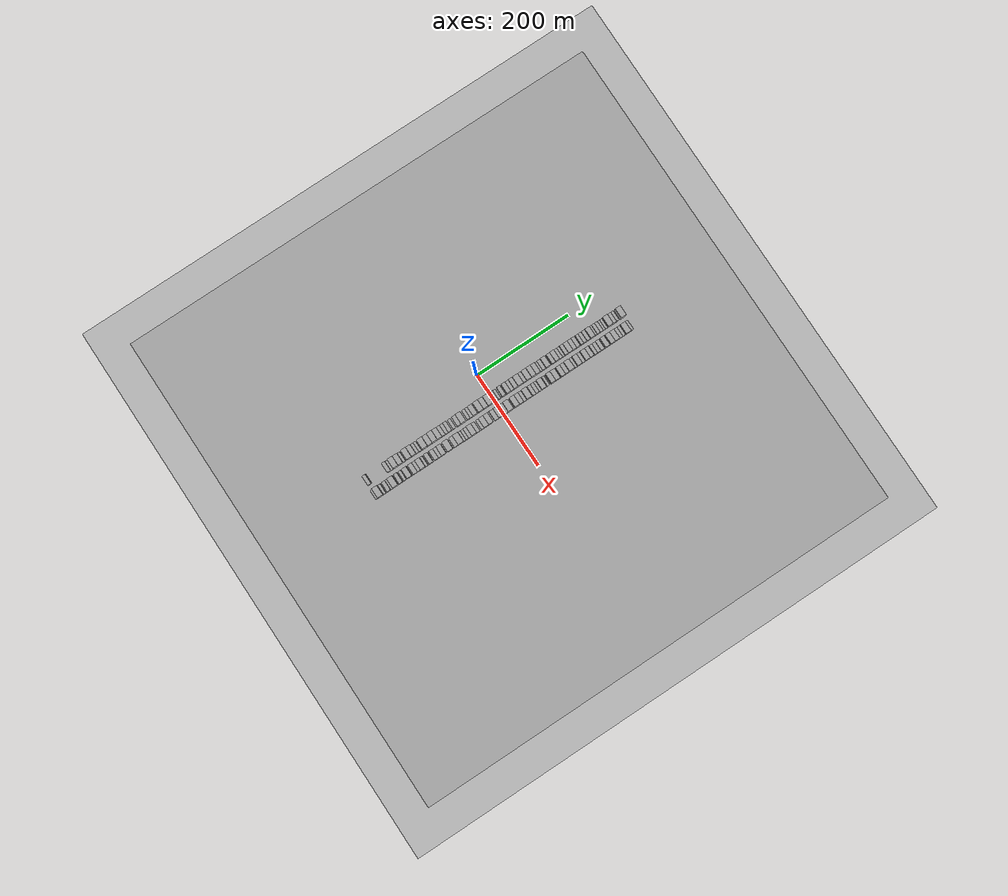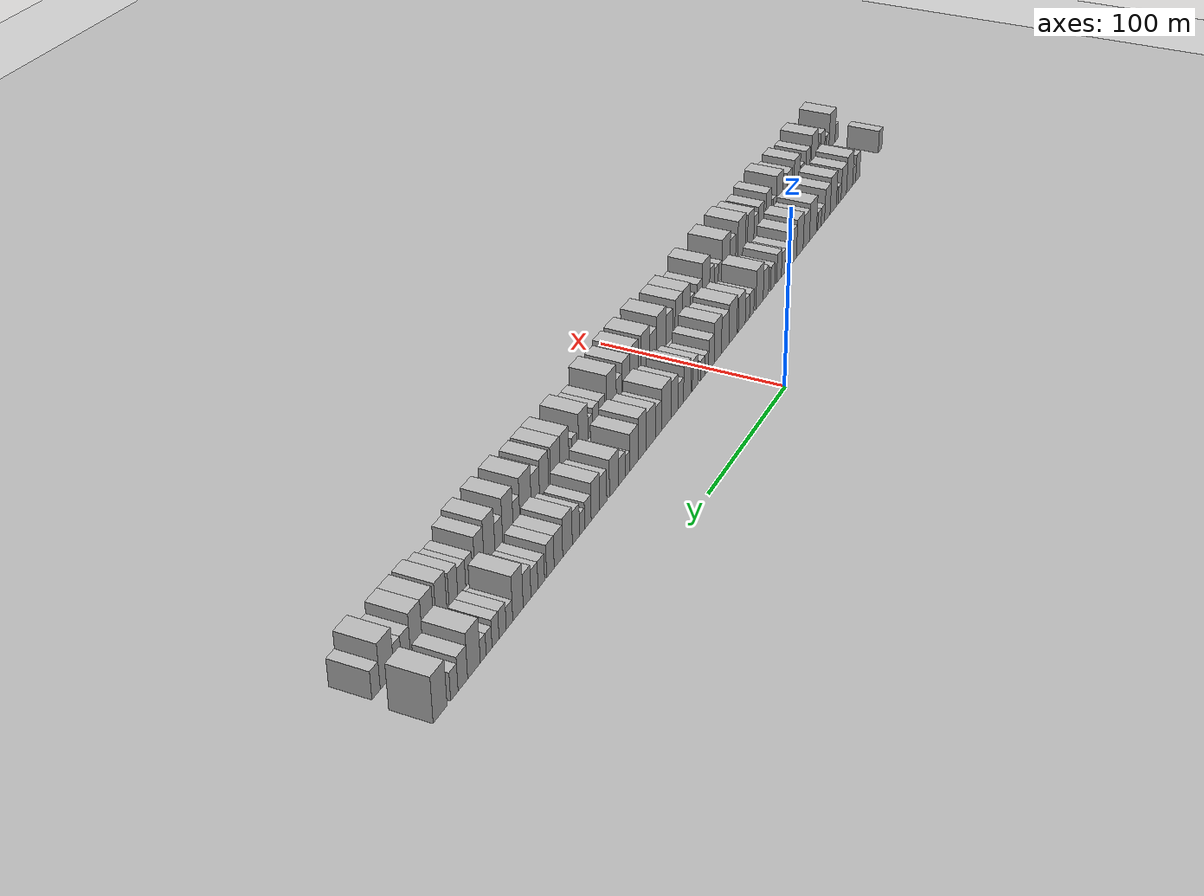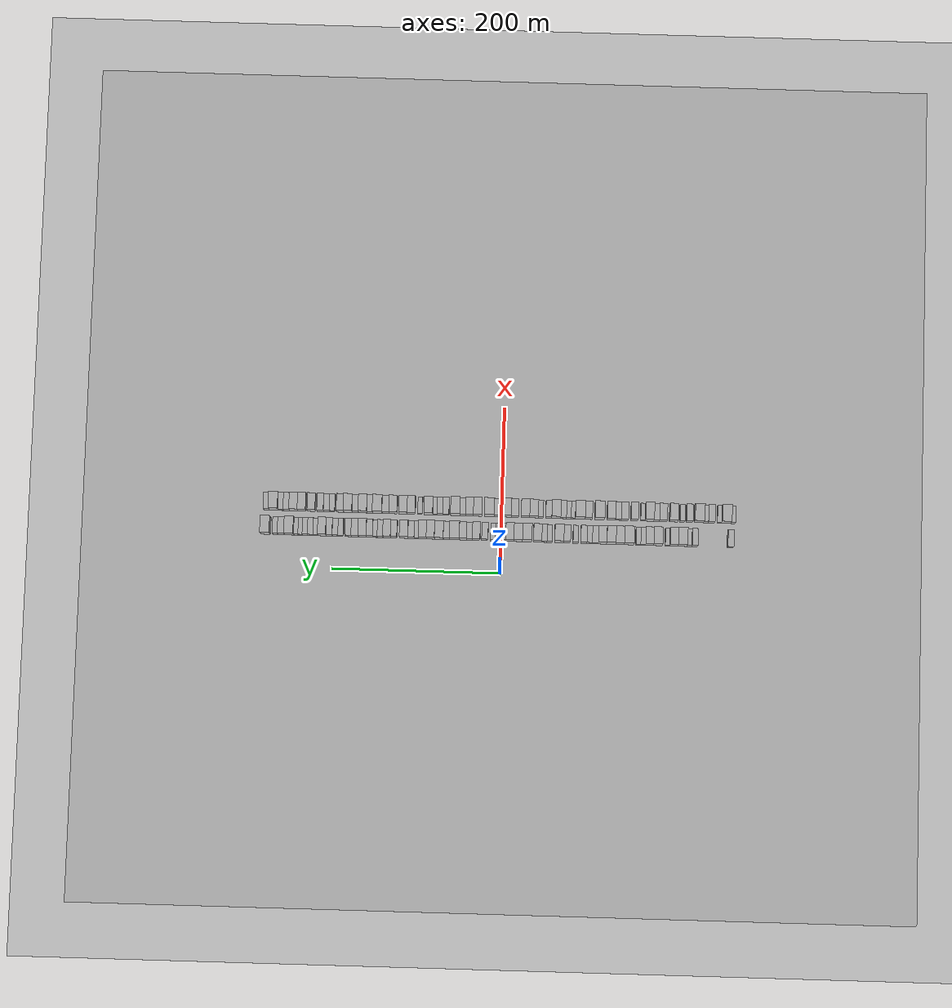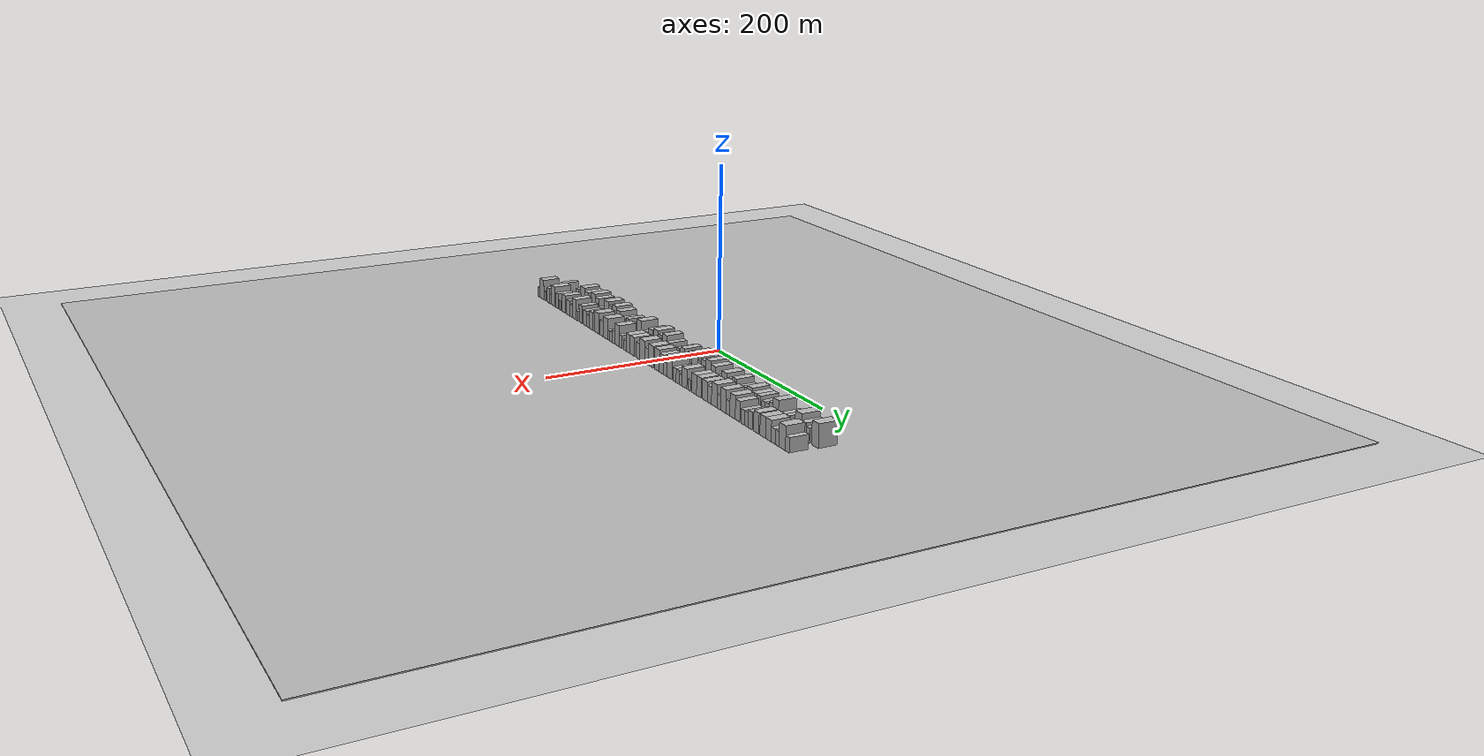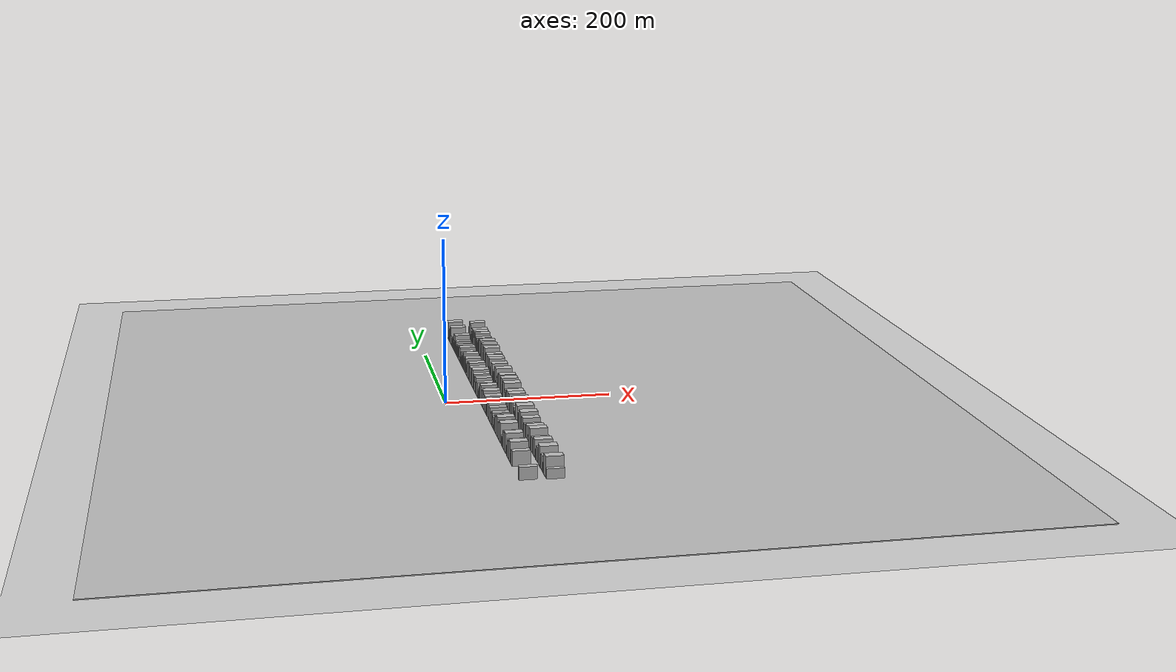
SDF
<?xml version="1.0" encoding="utf-8"?>

<sdf version="1.6">

   <world name="default">

      <gui fullscreen="0">

         <camera name="user_camera">

            <pose>-15 0 4.57585 0 0 0</pose>

            <view_controller>orbit</view_controller>

         </camera>

      </gui>

      <scene>

         <sky>

           <clouds>

             <speed>12</speed>

           </clouds>

         </sky>

         <ambient>0.4 0.4 0.4 1</ambient>

         <background>0.7 0.7 0.7 1</background>

         <shadows>1</shadows>

      </scene>

      <gravity>0 0 -9.8066</gravity>

      <magnetic_field>6e-06 2.3e-05 -4.2e-05</magnetic_field>

      <physics default="0" name="default_physics" type="ode">

         <ode>

            <solver>

               <type>quick</type>

               <iters>10</iters>

               <sor>1.0</sor>

               <use_dynamic_moi_rescaling>0</use_dynamic_moi_rescaling>

            </solver>

            <constraints>

               <cfm>0</cfm>

               <erp>0.2</erp>

               <contact_max_correcting_vel>100</contact_max_correcting_vel>

               <contact_surface_layer>0.001</contact_surface_layer>

            </constraints>

         </ode>

         <max_step_size>0.004</max_step_size>

         <real_time_factor>1</real_time_factor>

         <real_time_update_rate>250</real_time_update_rate>

      </physics>

      <light name="sun" type="directional">

         <cast_shadows>1</cast_shadows>

         <pose>0 0 10 0 0 0</pose>

         <diffuse>0.8 0.8 0.8 1</diffuse>

         <specular>0.2 0.2 0.2 1</specular>

         <attenuation>

            <range>1000</range>

            <constant>0.9</constant>

            <linear>0.01</linear>

            <quadratic>0.001</quadratic>

         </attenuation>

         <direction>-0.5 0.1 -0.9</direction>

      </light>

      <include>

         <name>ground_plane_1</name>

         <uri>model://HANNAS_ground_plane</uri>

         <pose>0 0 0  0 0 0</pose>

      </include>

      <include>

         <name>ground_plane_2</name>

         <uri>model://HANNAS_ground_plane</uri>

         <pose>100 0 0  0 0 0</pose>

      </include>

      <model name="building_1">

         <static>1</static>

         <pose frame="">50.0000 -272.4769 0 0.000000 0.000000 0.000000</pose>

         <link name="link">

            <pose frame="">0 0 7.50 0 0 0</pose>

            <collision name="collision">

               <geometry>

                  <box>

                     <size>20.0000 7.0463 15.0000</size>

                  </box>

               </geometry>

               <max_contacts>10</max_contacts>

               <surface>

                  <contact>

                     <ode/>

                  </contact>

                  <bounce/>

                  <friction>

                     <torsional>

                        <ode/>

                     </torsional>

                     <ode/>

                  </friction>

               </surface>

            </collision>

            <visual name="visual">

               <cast_shadows>0</cast_shadows>

               <geometry>

                  <box>

                     <size>20.0000 7.0463 15.0000</size>

                  </box>

               </geometry>

               <material>

                  <script>

                     <uri>model://HANNAS_wall/materials/scripts</uri>

                     <uri>model://HANNAS_wall/materials/textures</uri>

                     <name>vrc/HANNAS_wall</name>

                  </script>

               </material>

            </visual>

            <self_collide>0</self_collide>

            <enable_wind>0</enable_wind>

            <kinematic>0</kinematic>

         </link>

      </model>

      <model name="building_2">

         <static>1</static>

         <pose frame="">50.0000 -230.0296 0 0.000000 0.000000 0.000000</pose>

         <link name="link">

            <pose frame="">0 0 9.00 0 0 0</pose>

            <collision name="collision">

               <geometry>

                  <box>

                     <size>20.0000 7.2828 18.0000</size>

                  </box>

               </geometry>

               <max_contacts>10</max_contacts>

               <surface>

                  <contact>

                     <ode/>

                  </contact>

                  <bounce/>

                  <friction>

                     <torsional>

                        <ode/>

                     </torsional>

                     <ode/>

                  </friction>

               </surface>

            </collision>

            <visual name="visual">

               <cast_shadows>0</cast_shadows>

               <geometry>

                  <box>

                     <size>20.0000 7.2828 18.0000</size>

                  </box>

               </geometry>

               <material>

                  <script>

                     <uri>model://HANNAS_wall/materials/scripts</uri>

                     <uri>model://HANNAS_wall/materials/textures</uri>

                     <name>vrc/HANNAS_wall</name>

                  </script>

               </material>

            </visual>

            <self_collide>0</self_collide>

            <enable_wind>0</enable_wind>

            <kinematic>0</kinematic>

         </link>

      </model>

      <model name="building_3">

         <static>1</static>

         <pose frame="">50.0000 -223.5794 0 0.000000 0.000000 0.000000</pose>

         <link name="link">

            <pose frame="">0 0 6.00 0 0 0</pose>

            <collision name="collision">

               <geometry>

                  <box>

                     <size>20.0000 5.6176 12.0000</size>

                  </box>

               </geometry>

               <max_contacts>10</max_contacts>

               <surface>

                  <contact>

                     <ode/>

                  </contact>

                  <bounce/>

                  <friction>

                     <torsional>

                        <ode/>

                     </torsional>

                     <ode/>

                  </friction>

               </surface>

            </collision>

            <visual name="visual">

               <cast_shadows>0</cast_shadows>

               <geometry>

                  <box>

                     <size>20.0000 5.6176 12.0000</size>

                  </box>

               </geometry>

               <material>

                  <script>

                     <uri>model://HANNAS_wall/materials/scripts</uri>

                     <uri>model://HANNAS_wall/materials/textures</uri>

                     <name>vrc/HANNAS_wall</name>

                  </script>

               </material>

            </visual>

            <self_collide>0</self_collide>

            <enable_wind>0</enable_wind>

            <kinematic>0</kinematic>

         </link>

      </model>

      <model name="building_4">

         <static>1</static>

         <pose frame="">50.0000 -215.2634 0 0.000000 0.000000 0.000000</pose>

         <link name="link">

            <pose frame="">0 0 12.00 0 0 0</pose>

            <collision name="collision">

               <geometry>

                  <box>

                     <size>20.0000 11.0144 24.0000</size>

                  </box>

               </geometry>

               <max_contacts>10</max_contacts>

               <surface>

                  <contact>

                     <ode/>

                  </contact>

                  <bounce/>

                  <friction>

                     <torsional>

                        <ode/>

                     </torsional>

                     <ode/>

                  </friction>

               </surface>

            </collision>

            <visual name="visual">

               <cast_shadows>0</cast_shadows>

               <geometry>

                  <box>

                     <size>20.0000 11.0144 24.0000</size>

                  </box>

               </geometry>

               <material>

                  <script>

                     <uri>model://HANNAS_wall/materials/scripts</uri>

                     <uri>model://HANNAS_wall/materials/textures</uri>

                     <name>vrc/HANNAS_wall</name>

                  </script>

               </material>

            </visual>

            <self_collide>0</self_collide>

            <enable_wind>0</enable_wind>

            <kinematic>0</kinematic>

         </link>

      </model>

      <model name="building_5">

         <static>1</static>

         <pose frame="">50.0000 -204.9244 0 0.000000 0.000000 0.000000</pose>

         <link name="link">

            <pose frame="">0 0 10.50 0 0 0</pose>

            <collision name="collision">

               <geometry>

                  <box>

                     <size>20.0000 9.6638 21.0000</size>

                  </box>

               </geometry>

               <max_contacts>10</max_contacts>

               <surface>

                  <contact>

                     <ode/>

                  </contact>

                  <bounce/>

                  <friction>

                     <torsional>

                        <ode/>

                     </torsional>

                     <ode/>

                  </friction>

               </surface>

            </collision>

            <visual name="visual">

               <cast_shadows>0</cast_shadows>

               <geometry>

                  <box>

                     <size>20.0000 9.6638 21.0000</size>

                  </box>

               </geometry>

               <material>

                  <script>

                     <uri>model://HANNAS_wall/materials/scripts</uri>

                     <uri>model://HANNAS_wall/materials/textures</uri>

                     <name>vrc/HANNAS_wall</name>

                  </script>

               </material>

            </visual>

            <self_collide>0</self_collide>

            <enable_wind>0</enable_wind>

            <kinematic>0</kinematic>

         </link>

      </model>

      <model name="building_6">

         <static>1</static>

         <pose frame="">50.0000 -197.4030 0 0.000000 0.000000 0.000000</pose>

         <link name="link">

            <pose frame="">0 0 6.00 0 0 0</pose>

            <collision name="collision">

               <geometry>

                  <box>

                     <size>20.0000 5.3790 12.0000</size>

                  </box>

               </geometry>

               <max_contacts>10</max_contacts>

               <surface>

                  <contact>

                     <ode/>

                  </contact>

                  <bounce/>

                  <friction>

                     <torsional>

                        <ode/>

                     </torsional>

                     <ode/>

                  </friction>

               </surface>

            </collision>

            <visual name="visual">

               <cast_shadows>0</cast_shadows>

               <geometry>

                  <box>

                     <size>20.0000 5.3790 12.0000</size>

                  </box>

               </geometry>

               <material>

                  <script>

                     <uri>model://HANNAS_wall/materials/scripts</uri>

                     <uri>model://HANNAS_wall/materials/textures</uri>

                     <name>vrc/HANNAS_wall</name>

                  </script>

               </material>

            </visual>

            <self_collide>0</self_collide>

            <enable_wind>0</enable_wind>

            <kinematic>0</kinematic>

         </link>

      </model>

      <model name="building_7">

         <static>1</static>

         <pose frame="">50.0000 -186.3632 0 0.000000 0.000000 0.000000</pose>

         <link name="link">

            <pose frame="">0 0 12.00 0 0 0</pose>

            <collision name="collision">

               <geometry>

                  <box>

                     <size>20.0000 10.7004 24.0000</size>

                  </box>

               </geometry>

               <max_contacts>10</max_contacts>

               <surface>

                  <contact>

                     <ode/>

                  </contact>

                  <bounce/>

                  <friction>

                     <torsional>

                        <ode/>

                     </torsional>

                     <ode/>

                  </friction>

               </surface>

            </collision>

            <visual name="visual">

               <cast_shadows>0</cast_shadows>

               <geometry>

                  <box>

                     <size>20.0000 10.7004 24.0000</size>

                  </box>

               </geometry>

               <material>

                  <script>

                     <uri>model://HANNAS_wall/materials/scripts</uri>

                     <uri>model://HANNAS_wall/materials/textures</uri>

                     <name>vrc/HANNAS_wall</name>

                  </script>

               </material>

            </visual>

            <self_collide>0</self_collide>

            <enable_wind>0</enable_wind>

            <kinematic>0</kinematic>

         </link>

      </model>

      <model name="building_8">

         <static>1</static>

         <pose frame="">50.0000 -176.3072 0 0.000000 0.000000 0.000000</pose>

         <link name="link">

            <pose frame="">0 0 10.50 0 0 0</pose>

            <collision name="collision">

               <geometry>

                  <box>

                     <size>20.0000 9.4116 21.0000</size>

                  </box>

               </geometry>

               <max_contacts>10</max_contacts>

               <surface>

                  <contact>

                     <ode/>

                  </contact>

                  <bounce/>

                  <friction>

                     <torsional>

                        <ode/>

                     </torsional>

                     <ode/>

                  </friction>

               </surface>

            </collision>

            <visual name="visual">

               <cast_shadows>0</cast_shadows>

               <geometry>

                  <box>

                     <size>20.0000 9.4116 21.0000</size>

                  </box>

               </geometry>

               <material>

                  <script>

                     <uri>model://HANNAS_wall/materials/scripts</uri>

                     <uri>model://HANNAS_wall/materials/textures</uri>

                     <name>vrc/HANNAS_wall</name>

                  </script>

               </material>

            </visual>

            <self_collide>0</self_collide>

            <enable_wind>0</enable_wind>

            <kinematic>0</kinematic>

         </link>

      </model>

      <model name="building_9">

         <static>1</static>

         <pose frame="">50.0000 -168.6208 0 0.000000 0.000000 0.000000</pose>

         <link name="link">

            <pose frame="">0 0 6.00 0 0 0</pose>

            <collision name="collision">

               <geometry>

                  <box>

                     <size>20.0000 5.9611 12.0000</size>

                  </box>

               </geometry>

               <max_contacts>10</max_contacts>

               <surface>

                  <contact>

                     <ode/>

                  </contact>

                  <bounce/>

                  <friction>

                     <torsional>

                        <ode/>

                     </torsional>

                     <ode/>

                  </friction>

               </surface>

            </collision>

            <visual name="visual">

               <cast_shadows>0</cast_shadows>

               <geometry>

                  <box>

                     <size>20.0000 5.9611 12.0000</size>

                  </box>

               </geometry>

               <material>

                  <script>

                     <uri>model://HANNAS_wall/materials/scripts</uri>

                     <uri>model://HANNAS_wall/materials/textures</uri>

                     <name>vrc/HANNAS_wall</name>

                  </script>

               </material>

            </visual>

            <self_collide>0</self_collide>

            <enable_wind>0</enable_wind>

            <kinematic>0</kinematic>

         </link>

      </model>

      <model name="building_10">

         <static>1</static>

         <pose frame="">50.0000 -162.8003 0 0.000000 0.000000 0.000000</pose>

         <link name="link">

            <pose frame="">0 0 6.00 0 0 0</pose>

            <collision name="collision">

               <geometry>

                  <box>

                     <size>20.0000 5.6799 12.0000</size>

                  </box>

               </geometry>

               <max_contacts>10</max_contacts>

               <surface>

                  <contact>

                     <ode/>

                  </contact>

                  <bounce/>

                  <friction>

                     <torsional>

                        <ode/>

                     </torsional>

                     <ode/>

                  </friction>

               </surface>

            </collision>

            <visual name="visual">

               <cast_shadows>0</cast_shadows>

               <geometry>

                  <box>

                     <size>20.0000 5.6799 12.0000</size>

                  </box>

               </geometry>

               <material>

                  <script>

                     <uri>model://HANNAS_wall/materials/scripts</uri>

                     <uri>model://HANNAS_wall/materials/textures</uri>

                     <name>vrc/HANNAS_wall</name>

                  </script>

               </material>

            </visual>

            <self_collide>0</self_collide>

            <enable_wind>0</enable_wind>

            <kinematic>0</kinematic>

         </link>

      </model>

      <model name="building_11">

         <static>1</static>

         <pose frame="">50.0000 -152.1003 0 0.000000 0.000000 0.000000</pose>

         <link name="link">

            <pose frame="">0 0 12.00 0 0 0</pose>

            <collision name="collision">

               <geometry>

                  <box>

                     <size>20.0000 11.7200 24.0000</size>

                  </box>

               </geometry>

               <max_contacts>10</max_contacts>

               <surface>

                  <contact>

                     <ode/>

                  </contact>

                  <bounce/>

                  <friction>

                     <torsional>

                        <ode/>

                     </torsional>

                     <ode/>

                  </friction>

               </surface>

            </collision>

            <visual name="visual">

               <cast_shadows>0</cast_shadows>

               <geometry>

                  <box>

                     <size>20.0000 11.7200 24.0000</size>

                  </box>

               </geometry>

               <material>

                  <script>

                     <uri>model://HANNAS_wall/materials/scripts</uri>

                     <uri>model://HANNAS_wall/materials/textures</uri>

                     <name>vrc/HANNAS_wall</name>

                  </script>

               </material>

            </visual>

            <self_collide>0</self_collide>

            <enable_wind>0</enable_wind>

            <kinematic>0</kinematic>

         </link>

      </model>

      <model name="building_12">

         <static>1</static>

         <pose frame="">50.0000 -141.1149 0 0.000000 0.000000 0.000000</pose>

         <link name="link">

            <pose frame="">0 0 10.50 0 0 0</pose>

            <collision name="collision">

               <geometry>

                  <box>

                     <size>20.0000 10.2509 21.0000</size>

                  </box>

               </geometry>

               <max_contacts>10</max_contacts>

               <surface>

                  <contact>

                     <ode/>

                  </contact>

                  <bounce/>

                  <friction>

                     <torsional>

                        <ode/>

                     </torsional>

                     <ode/>

                  </friction>

               </surface>

            </collision>

            <visual name="visual">

               <cast_shadows>0</cast_shadows>

               <geometry>

                  <box>

                     <size>20.0000 10.2509 21.0000</size>

                  </box>

               </geometry>

               <material>

                  <script>

                     <uri>model://HANNAS_wall/materials/scripts</uri>

                     <uri>model://HANNAS_wall/materials/textures</uri>

                     <name>vrc/HANNAS_wall</name>

                  </script>

               </material>

            </visual>

            <self_collide>0</self_collide>

            <enable_wind>0</enable_wind>

            <kinematic>0</kinematic>

         </link>

      </model>

      <model name="building_13">

         <static>1</static>

         <pose frame="">50.0000 -130.6137 0 0.000000 0.000000 0.000000</pose>

         <link name="link">

            <pose frame="">0 0 12.00 0 0 0</pose>

            <collision name="collision">

               <geometry>

                  <box>

                     <size>20.0000 10.7514 24.0000</size>

                  </box>

               </geometry>

               <max_contacts>10</max_contacts>

               <surface>

                  <contact>

                     <ode/>

                  </contact>

                  <bounce/>

                  <friction>

                     <torsional>

                        <ode/>

                     </torsional>

                     <ode/>

                  </friction>

               </surface>

            </collision>

            <visual name="visual">

               <cast_shadows>0</cast_shadows>

               <geometry>

                  <box>

                     <size>20.0000 10.7514 24.0000</size>

                  </box>

               </geometry>

               <material>

                  <script>

                     <uri>model://HANNAS_wall/materials/scripts</uri>

                     <uri>model://HANNAS_wall/materials/textures</uri>

                     <name>vrc/HANNAS_wall</name>

                  </script>

               </material>

            </visual>

            <self_collide>0</self_collide>

            <enable_wind>0</enable_wind>

            <kinematic>0</kinematic>

         </link>

      </model>

      <model name="building_14">

         <static>1</static>

         <pose frame="">50.0000 -120.3150 0 0.000000 0.000000 0.000000</pose>

         <link name="link">

            <pose frame="">0 0 10.50 0 0 0</pose>

            <collision name="collision">

               <geometry>

                  <box>

                     <size>20.0000 9.8462 21.0000</size>

                  </box>

               </geometry>

               <max_contacts>10</max_contacts>

               <surface>

                  <contact>

                     <ode/>

                  </contact>

                  <bounce/>

                  <friction>

                     <torsional>

                        <ode/>

                     </torsional>

                     <ode/>

                  </friction>

               </surface>

            </collision>

            <visual name="visual">

               <cast_shadows>0</cast_shadows>

               <geometry>

                  <box>

                     <size>20.0000 9.8462 21.0000</size>

                  </box>

               </geometry>

               <material>

                  <script>

                     <uri>model://HANNAS_wall/materials/scripts</uri>

                     <uri>model://HANNAS_wall/materials/textures</uri>

                     <name>vrc/HANNAS_wall</name>

                  </script>

               </material>

            </visual>

            <self_collide>0</self_collide>

            <enable_wind>0</enable_wind>

            <kinematic>0</kinematic>

         </link>

      </model>

      <model name="building_15">

         <static>1</static>

         <pose frame="">50.0000 -111.7804 0 0.000000 0.000000 0.000000</pose>

         <link name="link">

            <pose frame="">0 0 7.50 0 0 0</pose>

            <collision name="collision">

               <geometry>

                  <box>

                     <size>20.0000 7.2230 15.0000</size>

                  </box>

               </geometry>

               <max_contacts>10</max_contacts>

               <surface>

                  <contact>

                     <ode/>

                  </contact>

                  <bounce/>

                  <friction>

                     <torsional>

                        <ode/>

                     </torsional>

                     <ode/>

                  </friction>

               </surface>

            </collision>

            <visual name="visual">

               <cast_shadows>0</cast_shadows>

               <geometry>

                  <box>

                     <size>20.0000 7.2230 15.0000</size>

                  </box>

               </geometry>

               <material>

                  <script>

                     <uri>model://HANNAS_wall/materials/scripts</uri>

                     <uri>model://HANNAS_wall/materials/textures</uri>

                     <name>vrc/HANNAS_wall</name>

                  </script>

               </material>

            </visual>

            <self_collide>0</self_collide>

            <enable_wind>0</enable_wind>

            <kinematic>0</kinematic>

         </link>

      </model>

      <model name="building_16">

         <static>1</static>

         <pose frame="">50.0000 -104.9020 0 0.000000 0.000000 0.000000</pose>

         <link name="link">

            <pose frame="">0 0 7.50 0 0 0</pose>

            <collision name="collision">

               <geometry>

                  <box>

                     <size>20.0000 6.5338 15.0000</size>

                  </box>

               </geometry>

               <max_contacts>10</max_contacts>

               <surface>

                  <contact>

                     <ode/>

                  </contact>

                  <bounce/>

                  <friction>

                     <torsional>

                        <ode/>

                     </torsional>

                     <ode/>

                  </friction>

               </surface>

            </collision>

            <visual name="visual">

               <cast_shadows>0</cast_shadows>

               <geometry>

                  <box>

                     <size>20.0000 6.5338 15.0000</size>

                  </box>

               </geometry>

               <material>

                  <script>

                     <uri>model://HANNAS_wall/materials/scripts</uri>

                     <uri>model://HANNAS_wall/materials/textures</uri>

                     <name>vrc/HANNAS_wall</name>

                  </script>

               </material>

            </visual>

            <self_collide>0</self_collide>

            <enable_wind>0</enable_wind>

            <kinematic>0</kinematic>

         </link>

      </model>

      <model name="building_17">

         <static>1</static>

         <pose frame="">50.0000 -98.0287 0 0.000000 0.000000 0.000000</pose>

         <link name="link">

            <pose frame="">0 0 9.00 0 0 0</pose>

            <collision name="collision">

               <geometry>

                  <box>

                     <size>20.0000 7.2128 18.0000</size>

                  </box>

               </geometry>

               <max_contacts>10</max_contacts>

               <surface>

                  <contact>

                     <ode/>

                  </contact>

                  <bounce/>

                  <friction>

                     <torsional>

                        <ode/>

                     </torsional>

                     <ode/>

                  </friction>

               </surface>

            </collision>

            <visual name="visual">

               <cast_shadows>0</cast_shadows>

               <geometry>

                  <box>

                     <size>20.0000 7.2128 18.0000</size>

                  </box>

               </geometry>

               <material>

                  <script>

                     <uri>model://HANNAS_wall/materials/scripts</uri>

                     <uri>model://HANNAS_wall/materials/textures</uri>

                     <name>vrc/HANNAS_wall</name>

                  </script>

               </material>

            </visual>

            <self_collide>0</self_collide>

            <enable_wind>0</enable_wind>

            <kinematic>0</kinematic>

         </link>

      </model>

      <model name="building_18">

         <static>1</static>

         <pose frame="">50.0000 -88.2988 0 0.000000 0.000000 0.000000</pose>

         <link name="link">

            <pose frame="">0 0 7.50 0 0 0</pose>

            <collision name="collision">

               <geometry>

                  <box>

                     <size>20.0000 6.2469 15.0000</size>

                  </box>

               </geometry>

               <max_contacts>10</max_contacts>

               <surface>

                  <contact>

                     <ode/>

                  </contact>

                  <bounce/>

                  <friction>

                     <torsional>

                        <ode/>

                     </torsional>

                     <ode/>

                  </friction>

               </surface>

            </collision>

            <visual name="visual">

               <cast_shadows>0</cast_shadows>

               <geometry>

                  <box>

                     <size>20.0000 6.2469 15.0000</size>

                  </box>

               </geometry>

               <material>

                  <script>

                     <uri>model://HANNAS_wall/materials/scripts</uri>

                     <uri>model://HANNAS_wall/materials/textures</uri>

                     <name>vrc/HANNAS_wall</name>

                  </script>

               </material>

            </visual>

            <self_collide>0</self_collide>

            <enable_wind>0</enable_wind>

            <kinematic>0</kinematic>

         </link>

      </model>

      <model name="building_19">

         <static>1</static>

         <pose frame="">50.0000 -78.1721 0 0.000000 0.000000 0.000000</pose>

         <link name="link">

            <pose frame="">0 0 9.00 0 0 0</pose>

            <collision name="collision">

               <geometry>

                  <box>

                     <size>20.0000 8.0066 18.0000</size>

                  </box>

               </geometry>

               <max_contacts>10</max_contacts>

               <surface>

                  <contact>

                     <ode/>

                  </contact>

                  <bounce/>

                  <friction>

                     <torsional>

                        <ode/>

                     </torsional>

                     <ode/>

                  </friction>

               </surface>

            </collision>

            <visual name="visual">

               <cast_shadows>0</cast_shadows>

               <geometry>

                  <box>

                     <size>20.0000 8.0066 18.0000</size>

                  </box>

               </geometry>

               <material>

                  <script>

                     <uri>model://HANNAS_wall/materials/scripts</uri>

                     <uri>model://HANNAS_wall/materials/textures</uri>

                     <name>vrc/HANNAS_wall</name>

                  </script>

               </material>

            </visual>

            <self_collide>0</self_collide>

            <enable_wind>0</enable_wind>

            <kinematic>0</kinematic>

         </link>

      </model>

      <model name="building_20">

         <static>1</static>

         <pose frame="">50.0000 -68.7891 0 0.000000 0.000000 0.000000</pose>

         <link name="link">

            <pose frame="">0 0 12.00 0 0 0</pose>

            <collision name="collision">

               <geometry>

                  <box>

                     <size>20.0000 10.7592 24.0000</size>

                  </box>

               </geometry>

               <max_contacts>10</max_contacts>

               <surface>

                  <contact>

                     <ode/>

                  </contact>

                  <bounce/>

                  <friction>

                     <torsional>

                        <ode/>

                     </torsional>

                     <ode/>

                  </friction>

               </surface>

            </collision>

            <visual name="visual">

               <cast_shadows>0</cast_shadows>

               <geometry>

                  <box>

                     <size>20.0000 10.7592 24.0000</size>

                  </box>

               </geometry>

               <material>

                  <script>

                     <uri>model://HANNAS_wall/materials/scripts</uri>

                     <uri>model://HANNAS_wall/materials/textures</uri>

                     <name>vrc/HANNAS_wall</name>

                  </script>

               </material>

            </visual>

            <self_collide>0</self_collide>

            <enable_wind>0</enable_wind>

            <kinematic>0</kinematic>

         </link>

      </model>

      <model name="building_21">

         <static>1</static>

         <pose frame="">50.0000 -57.3385 0 0.000000 0.000000 0.000000</pose>

         <link name="link">

            <pose frame="">0 0 7.50 0 0 0</pose>

            <collision name="collision">

               <geometry>

                  <box>

                     <size>20.0000 6.1420 15.0000</size>

                  </box>

               </geometry>

               <max_contacts>10</max_contacts>

               <surface>

                  <contact>

                     <ode/>

                  </contact>

                  <bounce/>

                  <friction>

                     <torsional>

                        <ode/>

                     </torsional>

                     <ode/>

                  </friction>

               </surface>

            </collision>

            <visual name="visual">

               <cast_shadows>0</cast_shadows>

               <geometry>

                  <box>

                     <size>20.0000 6.1420 15.0000</size>

                  </box>

               </geometry>

               <material>

                  <script>

                     <uri>model://HANNAS_wall/materials/scripts</uri>

                     <uri>model://HANNAS_wall/materials/textures</uri>

                     <name>vrc/HANNAS_wall</name>

                  </script>

               </material>

            </visual>

            <self_collide>0</self_collide>

            <enable_wind>0</enable_wind>

            <kinematic>0</kinematic>

         </link>

      </model>

      <model name="building_22">

         <static>1</static>

         <pose frame="">50.0000 -51.1925 0 0.000000 0.000000 0.000000</pose>

         <link name="link">

            <pose frame="">0 0 7.50 0 0 0</pose>

            <collision name="collision">

               <geometry>

                  <box>

                     <size>20.0000 6.1499 15.0000</size>

                  </box>

               </geometry>

               <max_contacts>10</max_contacts>

               <surface>

                  <contact>

                     <ode/>

                  </contact>

                  <bounce/>

                  <friction>

                     <torsional>

                        <ode/>

                     </torsional>

                     <ode/>

                  </friction>

               </surface>

            </collision>

            <visual name="visual">

               <cast_shadows>0</cast_shadows>

               <geometry>

                  <box>

                     <size>20.0000 6.1499 15.0000</size>

                  </box>

               </geometry>

               <material>

                  <script>

                     <uri>model://HANNAS_wall/materials/scripts</uri>

                     <uri>model://HANNAS_wall/materials/textures</uri>

                     <name>vrc/HANNAS_wall</name>

                  </script>

               </material>

            </visual>

            <self_collide>0</self_collide>

            <enable_wind>0</enable_wind>

            <kinematic>0</kinematic>

         </link>

      </model>

      <model name="building_23">

         <static>1</static>

         <pose frame="">50.0000 -43.2024 0 0.000000 0.000000 0.000000</pose>

         <link name="link">

            <pose frame="">0 0 10.50 0 0 0</pose>

            <collision name="collision">

               <geometry>

                  <box>

                     <size>20.0000 9.8303 21.0000</size>

                  </box>

               </geometry>

               <max_contacts>10</max_contacts>

               <surface>

                  <contact>

                     <ode/>

                  </contact>

                  <bounce/>

                  <friction>

                     <torsional>

                        <ode/>

                     </torsional>

                     <ode/>

                  </friction>

               </surface>

            </collision>

            <visual name="visual">

               <cast_shadows>0</cast_shadows>

               <geometry>

                  <box>

                     <size>20.0000 9.8303 21.0000</size>

                  </box>

               </geometry>

               <material>

                  <script>

                     <uri>model://HANNAS_wall/materials/scripts</uri>

                     <uri>model://HANNAS_wall/materials/textures</uri>

                     <name>vrc/HANNAS_wall</name>

                  </script>

               </material>

            </visual>

            <self_collide>0</self_collide>

            <enable_wind>0</enable_wind>

            <kinematic>0</kinematic>

         </link>

      </model>

      <model name="building_24">

         <static>1</static>

         <pose frame="">50.0000 -30.7148 0 0.000000 0.000000 0.000000</pose>

         <link name="link">

            <pose frame="">0 0 12.00 0 0 0</pose>

            <collision name="collision">

               <geometry>

                  <box>

                     <size>20.0000 11.1449 24.0000</size>

                  </box>

               </geometry>

               <max_contacts>10</max_contacts>

               <surface>

                  <contact>

                     <ode/>

                  </contact>

                  <bounce/>

                  <friction>

                     <torsional>

                        <ode/>

                     </torsional>

                     <ode/>

                  </friction>

               </surface>

            </collision>

            <visual name="visual">

               <cast_shadows>0</cast_shadows>

               <geometry>

                  <box>

                     <size>20.0000 11.1449 24.0000</size>

                  </box>

               </geometry>

               <material>

                  <script>

                     <uri>model://HANNAS_wall/materials/scripts</uri>

                     <uri>model://HANNAS_wall/materials/textures</uri>

                     <name>vrc/HANNAS_wall</name>

                  </script>

               </material>

            </visual>

            <self_collide>0</self_collide>

            <enable_wind>0</enable_wind>

            <kinematic>0</kinematic>

         </link>

      </model>

      <model name="building_25">

         <static>1</static>

         <pose frame="">50.0000 -20.0643 0 0.000000 0.000000 0.000000</pose>

         <link name="link">

            <pose frame="">0 0 10.50 0 0 0</pose>

            <collision name="collision">

               <geometry>

                  <box>

                     <size>20.0000 10.1560 21.0000</size>

                  </box>

               </geometry>

               <max_contacts>10</max_contacts>

               <surface>

                  <contact>

                     <ode/>

                  </contact>

                  <bounce/>

                  <friction>

                     <torsional>

                        <ode/>

                     </torsional>

                     <ode/>

                  </friction>

               </surface>

            </collision>

            <visual name="visual">

               <cast_shadows>0</cast_shadows>

               <geometry>

                  <box>

                     <size>20.0000 10.1560 21.0000</size>

                  </box>

               </geometry>

               <material>

                  <script>

                     <uri>model://HANNAS_wall/materials/scripts</uri>

                     <uri>model://HANNAS_wall/materials/textures</uri>

                     <name>vrc/HANNAS_wall</name>

                  </script>

               </material>

            </visual>

            <self_collide>0</self_collide>

            <enable_wind>0</enable_wind>

            <kinematic>0</kinematic>

         </link>

      </model>

      <model name="building_26">

         <static>1</static>

         <pose frame="">50.0000 -10.1497 0 0.000000 0.000000 0.000000</pose>

         <link name="link">

            <pose frame="">0 0 12.00 0 0 0</pose>

            <collision name="collision">

               <geometry>

                  <box>

                     <size>20.0000 9.6733 24.0000</size>

                  </box>

               </geometry>

               <max_contacts>10</max_contacts>

               <surface>

                  <contact>

                     <ode/>

                  </contact>

                  <bounce/>

                  <friction>

                     <torsional>

                        <ode/>

                     </torsional>

                     <ode/>

                  </friction>

               </surface>

            </collision>

            <visual name="visual">

               <cast_shadows>0</cast_shadows>

               <geometry>

                  <box>

                     <size>20.0000 9.6733 24.0000</size>

                  </box>

               </geometry>

               <material>

                  <script>

                     <uri>model://HANNAS_wall/materials/scripts</uri>

                     <uri>model://HANNAS_wall/materials/textures</uri>

                     <name>vrc/HANNAS_wall</name>

                  </script>

               </material>

            </visual>

            <self_collide>0</self_collide>

            <enable_wind>0</enable_wind>

            <kinematic>0</kinematic>

         </link>

      </model>

      <model name="building_27">

         <static>1</static>

         <pose frame="">50.0000 -1.5976 0 0.000000 0.000000 0.000000</pose>

         <link name="link">

            <pose frame="">0 0 9.00 0 0 0</pose>

            <collision name="collision">

               <geometry>

                  <box>

                     <size>20.0000 7.4308 18.0000</size>

                  </box>

               </geometry>

               <max_contacts>10</max_contacts>

               <surface>

                  <contact>

                     <ode/>

                  </contact>

                  <bounce/>

                  <friction>

                     <torsional>

                        <ode/>

                     </torsional>

                     <ode/>

                  </friction>

               </surface>

            </collision>

            <visual name="visual">

               <cast_shadows>0</cast_shadows>

               <geometry>

                  <box>

                     <size>20.0000 7.4308 18.0000</size>

                  </box>

               </geometry>

               <material>

                  <script>

                     <uri>model://HANNAS_wall/materials/scripts</uri>

                     <uri>model://HANNAS_wall/materials/textures</uri>

                     <name>vrc/HANNAS_wall</name>

                  </script>

               </material>

            </visual>

            <self_collide>0</self_collide>

            <enable_wind>0</enable_wind>

            <kinematic>0</kinematic>

         </link>

      </model>

      <model name="building_28">

         <static>1</static>

         <pose frame="">50.0000 4.6349 0 0.000000 0.000000 0.000000</pose>

         <link name="link">

            <pose frame="">0 0 6.00 0 0 0</pose>

            <collision name="collision">

               <geometry>

                  <box>

                     <size>20.0000 5.0342 12.0000</size>

                  </box>

               </geometry>

               <max_contacts>10</max_contacts>

               <surface>

                  <contact>

                     <ode/>

                  </contact>

                  <bounce/>

                  <friction>

                     <torsional>

                        <ode/>

                     </torsional>

                     <ode/>

                  </friction>

               </surface>

            </collision>

            <visual name="visual">

               <cast_shadows>0</cast_shadows>

               <geometry>

                  <box>

                     <size>20.0000 5.0342 12.0000</size>

                  </box>

               </geometry>

               <material>

                  <script>

                     <uri>model://HANNAS_wall/materials/scripts</uri>

                     <uri>model://HANNAS_wall/materials/textures</uri>

                     <name>vrc/HANNAS_wall</name>

                  </script>

               </material>

            </visual>

            <self_collide>0</self_collide>

            <enable_wind>0</enable_wind>

            <kinematic>0</kinematic>

         </link>

      </model>

      <model name="building_29">

         <static>1</static>

         <pose frame="">50.0000 9.9856 0 0.000000 0.000000 0.000000</pose>

         <link name="link">

            <pose frame="">0 0 6.00 0 0 0</pose>

            <collision name="collision">

               <geometry>

                  <box>

                     <size>20.0000 5.6673 12.0000</size>

                  </box>

               </geometry>

               <max_contacts>10</max_contacts>

               <surface>

                  <contact>

                     <ode/>

                  </contact>

                  <bounce/>

                  <friction>

                     <torsional>

                        <ode/>

                     </torsional>

                     <ode/>

                  </friction>

               </surface>

            </collision>

            <visual name="visual">

               <cast_shadows>0</cast_shadows>

               <geometry>

                  <box>

                     <size>20.0000 5.6673 12.0000</size>

                  </box>

               </geometry>

               <material>

                  <script>

                     <uri>model://HANNAS_wall/materials/scripts</uri>

                     <uri>model://HANNAS_wall/materials/textures</uri>

                     <name>vrc/HANNAS_wall</name>

                  </script>

               </material>

            </visual>

            <self_collide>0</self_collide>

            <enable_wind>0</enable_wind>

            <kinematic>0</kinematic>

         </link>

      </model>

      <model name="building_30">

         <static>1</static>

         <pose frame="">50.0000 19.5542 0 0.000000 0.000000 0.000000</pose>

         <link name="link">

            <pose frame="">0 0 9.00 0 0 0</pose>

            <collision name="collision">

               <geometry>

                  <box>

                     <size>20.0000 7.4699 18.0000</size>

                  </box>

               </geometry>

               <max_contacts>10</max_contacts>

               <surface>

                  <contact>

                     <ode/>

                  </contact>

                  <bounce/>

                  <friction>

                     <torsional>

                        <ode/>

                     </torsional>

                     <ode/>

                  </friction>

               </surface>

            </collision>

            <visual name="visual">

               <cast_shadows>0</cast_shadows>

               <geometry>

                  <box>

                     <size>20.0000 7.4699 18.0000</size>

                  </box>

               </geometry>

               <material>

                  <script>

                     <uri>model://HANNAS_wall/materials/scripts</uri>

                     <uri>model://HANNAS_wall/materials/textures</uri>

                     <name>vrc/HANNAS_wall</name>

                  </script>

               </material>

            </visual>

            <self_collide>0</self_collide>

            <enable_wind>0</enable_wind>

            <kinematic>0</kinematic>

         </link>

      </model>

      <model name="building_31">

         <static>1</static>

         <pose frame="">50.0000 29.8147 0 0.000000 0.000000 0.000000</pose>

         <link name="link">

            <pose frame="">0 0 10.50 0 0 0</pose>

            <collision name="collision">

               <geometry>

                  <box>

                     <size>20.0000 9.0512 21.0000</size>

                  </box>

               </geometry>

               <max_contacts>10</max_contacts>

               <surface>

                  <contact>

                     <ode/>

                  </contact>

                  <bounce/>

                  <friction>

                     <torsional>

                        <ode/>

                     </torsional>

                     <ode/>

                  </friction>

               </surface>

            </collision>

            <visual name="visual">

               <cast_shadows>0</cast_shadows>

               <geometry>

                  <box>

                     <size>20.0000 9.0512 21.0000</size>

                  </box>

               </geometry>

               <material>

                  <script>

                     <uri>model://HANNAS_wall/materials/scripts</uri>

                     <uri>model://HANNAS_wall/materials/textures</uri>

                     <name>vrc/HANNAS_wall</name>

                  </script>

               </material>

            </visual>

            <self_collide>0</self_collide>

            <enable_wind>0</enable_wind>

            <kinematic>0</kinematic>

         </link>

      </model>

      <model name="building_32">

         <static>1</static>

         <pose frame="">50.0000 37.8138 0 0.000000 0.000000 0.000000</pose>

         <link name="link">

            <pose frame="">0 0 7.50 0 0 0</pose>

            <collision name="collision">

               <geometry>

                  <box>

                     <size>20.0000 6.9470 15.0000</size>

                  </box>

               </geometry>

               <max_contacts>10</max_contacts>

               <surface>

                  <contact>

                     <ode/>

                  </contact>

                  <bounce/>

                  <friction>

                     <torsional>

                        <ode/>

                     </torsional>

                     <ode/>

                  </friction>

               </surface>

            </collision>

            <visual name="visual">

               <cast_shadows>0</cast_shadows>

               <geometry>

                  <box>

                     <size>20.0000 6.9470 15.0000</size>

                  </box>

               </geometry>

               <material>

                  <script>

                     <uri>model://HANNAS_wall/materials/scripts</uri>

                     <uri>model://HANNAS_wall/materials/textures</uri>

                     <name>vrc/HANNAS_wall</name>

                  </script>

               </material>

            </visual>

            <self_collide>0</self_collide>

            <enable_wind>0</enable_wind>

            <kinematic>0</kinematic>

         </link>

      </model>

      <model name="building_33">

         <static>1</static>

         <pose frame="">50.0000 45.5488 0 0.000000 0.000000 0.000000</pose>

         <link name="link">

            <pose frame="">0 0 10.50 0 0 0</pose>

            <collision name="collision">

               <geometry>

                  <box>

                     <size>20.0000 8.5230 21.0000</size>

                  </box>

               </geometry>

               <max_contacts>10</max_contacts>

               <surface>

                  <contact>

                     <ode/>

                  </contact>

                  <bounce/>

                  <friction>

                     <torsional>

                        <ode/>

                     </torsional>

                     <ode/>

                  </friction>

               </surface>

            </collision>

            <visual name="visual">

               <cast_shadows>0</cast_shadows>

               <geometry>

                  <box>

                     <size>20.0000 8.5230 21.0000</size>

                  </box>

               </geometry>

               <material>

                  <script>

                     <uri>model://HANNAS_wall/materials/scripts</uri>

                     <uri>model://HANNAS_wall/materials/textures</uri>

                     <name>vrc/HANNAS_wall</name>

                  </script>

               </material>

            </visual>

            <self_collide>0</self_collide>

            <enable_wind>0</enable_wind>

            <kinematic>0</kinematic>

         </link>

      </model>

      <model name="building_34">

         <static>1</static>

         <pose frame="">50.0000 55.7005 0 0.000000 0.000000 0.000000</pose>

         <link name="link">

            <pose frame="">0 0 12.00 0 0 0</pose>

            <collision name="collision">

               <geometry>

                  <box>

                     <size>20.0000 11.7803 24.0000</size>

                  </box>

               </geometry>

               <max_contacts>10</max_contacts>

               <surface>

                  <contact>

                     <ode/>

                  </contact>

                  <bounce/>

                  <friction>

                     <torsional>

                        <ode/>

                     </torsional>

                     <ode/>

                  </friction>

               </surface>

            </collision>

            <visual name="visual">

               <cast_shadows>0</cast_shadows>

               <geometry>

                  <box>

                     <size>20.0000 11.7803 24.0000</size>

                  </box>

               </geometry>

               <material>

                  <script>

                     <uri>model://HANNAS_wall/materials/scripts</uri>

                     <uri>model://HANNAS_wall/materials/textures</uri>

                     <name>vrc/HANNAS_wall</name>

                  </script>

               </material>

            </visual>

            <self_collide>0</self_collide>

            <enable_wind>0</enable_wind>

            <kinematic>0</kinematic>

         </link>

      </model>

      <model name="building_35">

         <static>1</static>

         <pose frame="">50.0000 65.2430 0 0.000000 0.000000 0.000000</pose>

         <link name="link">

            <pose frame="">0 0 9.00 0 0 0</pose>

            <collision name="collision">

               <geometry>

                  <box>

                     <size>20.0000 7.3048 18.0000</size>

                  </box>

               </geometry>

               <max_contacts>10</max_contacts>

               <surface>

                  <contact>

                     <ode/>

                  </contact>

                  <bounce/>

                  <friction>

                     <torsional>

                        <ode/>

                     </torsional>

                     <ode/>

                  </friction>

               </surface>

            </collision>

            <visual name="visual">

               <cast_shadows>0</cast_shadows>

               <geometry>

                  <box>

                     <size>20.0000 7.3048 18.0000</size>

                  </box>

               </geometry>

               <material>

                  <script>

                     <uri>model://HANNAS_wall/materials/scripts</uri>

                     <uri>model://HANNAS_wall/materials/textures</uri>

                     <name>vrc/HANNAS_wall</name>

                  </script>

               </material>

            </visual>

            <self_collide>0</self_collide>

            <enable_wind>0</enable_wind>

            <kinematic>0</kinematic>

         </link>

      </model>

      <model name="building_36">

         <static>1</static>

         <pose frame="">50.0000 74.1311 0 0.000000 0.000000 0.000000</pose>

         <link name="link">

            <pose frame="">0 0 10.50 0 0 0</pose>

            <collision name="collision">

               <geometry>

                  <box>

                     <size>20.0000 10.4713 21.0000</size>

                  </box>

               </geometry>

               <max_contacts>10</max_contacts>

               <surface>

                  <contact>

                     <ode/>

                  </contact>

                  <bounce/>

                  <friction>

                     <torsional>

                        <ode/>

                     </torsional>

                     <ode/>

                  </friction>

               </surface>

            </collision>

            <visual name="visual">

               <cast_shadows>0</cast_shadows>

               <geometry>

                  <box>

                     <size>20.0000 10.4713 21.0000</size>

                  </box>

               </geometry>

               <material>

                  <script>

                     <uri>model://HANNAS_wall/materials/scripts</uri>

                     <uri>model://HANNAS_wall/materials/textures</uri>

                     <name>vrc/HANNAS_wall</name>

                  </script>

               </material>

            </visual>

            <self_collide>0</self_collide>

            <enable_wind>0</enable_wind>

            <kinematic>0</kinematic>

         </link>

      </model>

      <model name="building_37">

         <static>1</static>

         <pose frame="">50.0000 84.1854 0 0.000000 0.000000 0.000000</pose>

         <link name="link">

            <pose frame="">0 0 12.00 0 0 0</pose>

            <collision name="collision">

               <geometry>

                  <box>

                     <size>20.0000 9.6375 24.0000</size>

                  </box>

               </geometry>

               <max_contacts>10</max_contacts>

               <surface>

                  <contact>

                     <ode/>

                  </contact>

                  <bounce/>

                  <friction>

                     <torsional>

                        <ode/>

                     </torsional>

                     <ode/>

                  </friction>

               </surface>

            </collision>

            <visual name="visual">

               <cast_shadows>0</cast_shadows>

               <geometry>

                  <box>

                     <size>20.0000 9.6375 24.0000</size>

                  </box>

               </geometry>

               <material>

                  <script>

                     <uri>model://HANNAS_wall/materials/scripts</uri>

                     <uri>model://HANNAS_wall/materials/textures</uri>

                     <name>vrc/HANNAS_wall</name>

                  </script>

               </material>

            </visual>

            <self_collide>0</self_collide>

            <enable_wind>0</enable_wind>

            <kinematic>0</kinematic>

         </link>

      </model>

      <model name="building_38">

         <static>1</static>

         <pose frame="">50.0000 93.7305 0 0.000000 0.000000 0.000000</pose>

         <link name="link">

            <pose frame="">0 0 10.50 0 0 0</pose>

            <collision name="collision">

               <geometry>

                  <box>

                     <size>20.0000 9.4528 21.0000</size>

                  </box>

               </geometry>

               <max_contacts>10</max_contacts>

               <surface>

                  <contact>

                     <ode/>

                  </contact>

                  <bounce/>

                  <friction>

                     <torsional>

                        <ode/>

                     </torsional>

                     <ode/>

                  </friction>

               </surface>

            </collision>

            <visual name="visual">

               <cast_shadows>0</cast_shadows>

               <geometry>

                  <box>

                     <size>20.0000 9.4528 21.0000</size>

                  </box>

               </geometry>

               <material>

                  <script>

                     <uri>model://HANNAS_wall/materials/scripts</uri>

                     <uri>model://HANNAS_wall/materials/textures</uri>

                     <name>vrc/HANNAS_wall</name>

                  </script>

               </material>

            </visual>

            <self_collide>0</self_collide>

            <enable_wind>0</enable_wind>

            <kinematic>0</kinematic>

         </link>

      </model>

      <model name="building_39">

         <static>1</static>

         <pose frame="">50.0000 101.0435 0 0.000000 0.000000 0.000000</pose>

         <link name="link">

            <pose frame="">0 0 6.00 0 0 0</pose>

            <collision name="collision">

               <geometry>

                  <box>

                     <size>20.0000 5.1731 12.0000</size>

                  </box>

               </geometry>

               <max_contacts>10</max_contacts>

               <surface>

                  <contact>

                     <ode/>

                  </contact>

                  <bounce/>

                  <friction>

                     <torsional>

                        <ode/>

                     </torsional>

                     <ode/>

                  </friction>

               </surface>

            </collision>

            <visual name="visual">

               <cast_shadows>0</cast_shadows>

               <geometry>

                  <box>

                     <size>20.0000 5.1731 12.0000</size>

                  </box>

               </geometry>

               <material>

                  <script>

                     <uri>model://HANNAS_wall/materials/scripts</uri>

                     <uri>model://HANNAS_wall/materials/textures</uri>

                     <name>vrc/HANNAS_wall</name>

                  </script>

               </material>

            </visual>

            <self_collide>0</self_collide>

            <enable_wind>0</enable_wind>

            <kinematic>0</kinematic>

         </link>

      </model>

      <model name="building_40">

         <static>1</static>

         <pose frame="">50.0000 107.2192 0 0.000000 0.000000 0.000000</pose>

         <link name="link">

            <pose frame="">0 0 7.50 0 0 0</pose>

            <collision name="collision">

               <geometry>

                  <box>

                     <size>20.0000 7.1782 15.0000</size>

                  </box>

               </geometry>

               <max_contacts>10</max_contacts>

               <surface>

                  <contact>

                     <ode/>

                  </contact>

                  <bounce/>

                  <friction>

                     <torsional>

                        <ode/>

                     </torsional>

                     <ode/>

                  </friction>

               </surface>

            </collision>

            <visual name="visual">

               <cast_shadows>0</cast_shadows>

               <geometry>

                  <box>

                     <size>20.0000 7.1782 15.0000</size>

                  </box>

               </geometry>

               <material>

                  <script>

                     <uri>model://HANNAS_wall/materials/scripts</uri>

                     <uri>model://HANNAS_wall/materials/textures</uri>

                     <name>vrc/HANNAS_wall</name>

                  </script>

               </material>

            </visual>

            <self_collide>0</self_collide>

            <enable_wind>0</enable_wind>

            <kinematic>0</kinematic>

         </link>

      </model>

      <model name="building_41">

         <static>1</static>

         <pose frame="">50.0000 115.8828 0 0.000000 0.000000 0.000000</pose>

         <link name="link">

            <pose frame="">0 0 10.50 0 0 0</pose>

            <collision name="collision">

               <geometry>

                  <box>

                     <size>20.0000 10.1492 21.0000</size>

                  </box>

               </geometry>

               <max_contacts>10</max_contacts>

               <surface>

                  <contact>

                     <ode/>

                  </contact>

                  <bounce/>

                  <friction>

                     <torsional>

                        <ode/>

                     </torsional>

                     <ode/>

                  </friction>

               </surface>

            </collision>

            <visual name="visual">

               <cast_shadows>0</cast_shadows>

               <geometry>

                  <box>

                     <size>20.0000 10.1492 21.0000</size>

                  </box>

               </geometry>

               <material>

                  <script>

                     <uri>model://HANNAS_wall/materials/scripts</uri>

                     <uri>model://HANNAS_wall/materials/textures</uri>

                     <name>vrc/HANNAS_wall</name>

                  </script>

               </material>

            </visual>

            <self_collide>0</self_collide>

            <enable_wind>0</enable_wind>

            <kinematic>0</kinematic>

         </link>

      </model>

      <model name="building_42">

         <static>1</static>

         <pose frame="">50.0000 127.7314 0 0.000000 0.000000 0.000000</pose>

         <link name="link">

            <pose frame="">0 0 9.00 0 0 0</pose>

            <collision name="collision">

               <geometry>

                  <box>

                     <size>20.0000 7.5479 18.0000</size>

                  </box>

               </geometry>

               <max_contacts>10</max_contacts>

               <surface>

                  <contact>

                     <ode/>

                  </contact>

                  <bounce/>

                  <friction>

                     <torsional>

                        <ode/>

                     </torsional>

                     <ode/>

                  </friction>

               </surface>

            </collision>

            <visual name="visual">

               <cast_shadows>0</cast_shadows>

               <geometry>

                  <box>

                     <size>20.0000 7.5479 18.0000</size>

                  </box>

               </geometry>

               <material>

                  <script>

                     <uri>model://HANNAS_wall/materials/scripts</uri>

                     <uri>model://HANNAS_wall/materials/textures</uri>

                     <name>vrc/HANNAS_wall</name>

                  </script>

               </material>

            </visual>

            <self_collide>0</self_collide>

            <enable_wind>0</enable_wind>

            <kinematic>0</kinematic>

         </link>

      </model>

      <model name="building_43">

         <static>1</static>

         <pose frame="">50.0000 136.0665 0 0.000000 0.000000 0.000000</pose>

         <link name="link">

            <pose frame="">0 0 10.50 0 0 0</pose>

            <collision name="collision">

               <geometry>

                  <box>

                     <size>20.0000 9.1223 21.0000</size>

                  </box>

               </geometry>

               <max_contacts>10</max_contacts>

               <surface>

                  <contact>

                     <ode/>

                  </contact>

                  <bounce/>

                  <friction>

                     <torsional>

                        <ode/>

                     </torsional>

                     <ode/>

                  </friction>

               </surface>

            </collision>

            <visual name="visual">

               <cast_shadows>0</cast_shadows>

               <geometry>

                  <box>

                     <size>20.0000 9.1223 21.0000</size>

                  </box>

               </geometry>

               <material>

                  <script>

                     <uri>model://HANNAS_wall/materials/scripts</uri>

                     <uri>model://HANNAS_wall/materials/textures</uri>

                     <name>vrc/HANNAS_wall</name>

                  </script>

               </material>

            </visual>

            <self_collide>0</self_collide>

            <enable_wind>0</enable_wind>

            <kinematic>0</kinematic>

         </link>

      </model>

      <model name="building_44">

         <static>1</static>

         <pose frame="">50.0000 144.0214 0 0.000000 0.000000 0.000000</pose>

         <link name="link">

            <pose frame="">0 0 7.50 0 0 0</pose>

            <collision name="collision">

               <geometry>

                  <box>

                     <size>20.0000 6.7875 15.0000</size>

                  </box>

               </geometry>

               <max_contacts>10</max_contacts>

               <surface>

                  <contact>

                     <ode/>

                  </contact>

                  <bounce/>

                  <friction>

                     <torsional>

                        <ode/>

                     </torsional>

                     <ode/>

                  </friction>

               </surface>

            </collision>

            <visual name="visual">

               <cast_shadows>0</cast_shadows>

               <geometry>

                  <box>

                     <size>20.0000 6.7875 15.0000</size>

                  </box>

               </geometry>

               <material>

                  <script>

                     <uri>model://HANNAS_wall/materials/scripts</uri>

                     <uri>model://HANNAS_wall/materials/textures</uri>

                     <name>vrc/HANNAS_wall</name>

                  </script>

               </material>

            </visual>

            <self_collide>0</self_collide>

            <enable_wind>0</enable_wind>

            <kinematic>0</kinematic>

         </link>

      </model>

      <model name="building_45">

         <static>1</static>

         <pose frame="">50.0000 150.0881 0 0.000000 0.000000 0.000000</pose>

         <link name="link">

            <pose frame="">0 0 6.00 0 0 0</pose>

            <collision name="collision">

               <geometry>

                  <box>

                     <size>20.0000 5.3460 12.0000</size>

                  </box>

               </geometry>

               <max_contacts>10</max_contacts>

               <surface>

                  <contact>

                     <ode/>

                  </contact>

                  <bounce/>

                  <friction>

                     <torsional>

                        <ode/>

                     </torsional>

                     <ode/>

                  </friction>

               </surface>

            </collision>

            <visual name="visual">

               <cast_shadows>0</cast_shadows>

               <geometry>

                  <box>

                     <size>20.0000 5.3460 12.0000</size>

                  </box>

               </geometry>

               <material>

                  <script>

                     <uri>model://HANNAS_wall/materials/scripts</uri>

                     <uri>model://HANNAS_wall/materials/textures</uri>

                     <name>vrc/HANNAS_wall</name>

                  </script>

               </material>

            </visual>

            <self_collide>0</self_collide>

            <enable_wind>0</enable_wind>

            <kinematic>0</kinematic>

         </link>

      </model>

      <model name="building_46">

         <static>1</static>

         <pose frame="">50.0000 156.4604 0 0.000000 0.000000 0.000000</pose>

         <link name="link">

            <pose frame="">0 0 9.00 0 0 0</pose>

            <collision name="collision">

               <geometry>

                  <box>

                     <size>20.0000 7.3986 18.0000</size>

                  </box>

               </geometry>

               <max_contacts>10</max_contacts>

               <surface>

                  <contact>

                     <ode/>

                  </contact>

                  <bounce/>

                  <friction>

                     <torsional>

                        <ode/>

                     </torsional>

                     <ode/>

                  </friction>

               </surface>

            </collision>

            <visual name="visual">

               <cast_shadows>0</cast_shadows>

               <geometry>

                  <box>

                     <size>20.0000 7.3986 18.0000</size>

                  </box>

               </geometry>

               <material>

                  <script>

                     <uri>model://HANNAS_wall/materials/scripts</uri>

                     <uri>model://HANNAS_wall/materials/textures</uri>

                     <name>vrc/HANNAS_wall</name>

                  </script>

               </material>

            </visual>

            <self_collide>0</self_collide>

            <enable_wind>0</enable_wind>

            <kinematic>0</kinematic>

         </link>

      </model>

      <model name="building_47">

         <static>1</static>

         <pose frame="">50.0000 164.9951 0 0.000000 0.000000 0.000000</pose>

         <link name="link">

            <pose frame="">0 0 10.50 0 0 0</pose>

            <collision name="collision">

               <geometry>

                  <box>

                     <size>20.0000 9.6708 21.0000</size>

                  </box>

               </geometry>

               <max_contacts>10</max_contacts>

               <surface>

                  <contact>

                     <ode/>

                  </contact>

                  <bounce/>

                  <friction>

                     <torsional>

                        <ode/>

                     </torsional>

                     <ode/>

                  </friction>

               </surface>

            </collision>

            <visual name="visual">

               <cast_shadows>0</cast_shadows>

               <geometry>

                  <box>

                     <size>20.0000 9.6708 21.0000</size>

                  </box>

               </geometry>

               <material>

                  <script>

                     <uri>model://HANNAS_wall/materials/scripts</uri>

                     <uri>model://HANNAS_wall/materials/textures</uri>

                     <name>vrc/HANNAS_wall</name>

                  </script>

               </material>

            </visual>

            <self_collide>0</self_collide>

            <enable_wind>0</enable_wind>

            <kinematic>0</kinematic>

         </link>

      </model>

      <model name="building_48">

         <static>1</static>

         <pose frame="">50.0000 174.0774 0 0.000000 0.000000 0.000000</pose>

         <link name="link">

            <pose frame="">0 0 9.00 0 0 0</pose>

            <collision name="collision">

               <geometry>

                  <box>

                     <size>20.0000 8.4938 18.0000</size>

                  </box>

               </geometry>

               <max_contacts>10</max_contacts>

               <surface>

                  <contact>

                     <ode/>

                  </contact>

                  <bounce/>

                  <friction>

                     <torsional>

                        <ode/>

                     </torsional>

                     <ode/>

                  </friction>

               </surface>

            </collision>

            <visual name="visual">

               <cast_shadows>0</cast_shadows>

               <geometry>

                  <box>

                     <size>20.0000 8.4938 18.0000</size>

                  </box>

               </geometry>

               <material>

                  <script>

                     <uri>model://HANNAS_wall/materials/scripts</uri>

                     <uri>model://HANNAS_wall/materials/textures</uri>

                     <name>vrc/HANNAS_wall</name>

                  </script>

               </material>

            </visual>

            <self_collide>0</self_collide>

            <enable_wind>0</enable_wind>

            <kinematic>0</kinematic>

         </link>

      </model>

      <model name="building_49">

         <static>1</static>

         <pose frame="">50.0000 182.0270 0 0.000000 0.000000 0.000000</pose>

         <link name="link">

            <pose frame="">0 0 9.00 0 0 0</pose>

            <collision name="collision">

               <geometry>

                  <box>

                     <size>20.0000 7.4053 18.0000</size>

                  </box>

               </geometry>

               <max_contacts>10</max_contacts>

               <surface>

                  <contact>

                     <ode/>

                  </contact>

                  <bounce/>

                  <friction>

                     <torsional>

                        <ode/>

                     </torsional>

                     <ode/>

                  </friction>

               </surface>

            </collision>

            <visual name="visual">

               <cast_shadows>0</cast_shadows>

               <geometry>

                  <box>

                     <size>20.0000 7.4053 18.0000</size>

                  </box>

               </geometry>

               <material>

                  <script>

                     <uri>model://HANNAS_wall/materials/scripts</uri>

                     <uri>model://HANNAS_wall/materials/textures</uri>

                     <name>vrc/HANNAS_wall</name>

                  </script>

               </material>

            </visual>

            <self_collide>0</self_collide>

            <enable_wind>0</enable_wind>

            <kinematic>0</kinematic>

         </link>

      </model>

      <model name="building_50">

         <static>1</static>

         <pose frame="">50.0000 190.8925 0 0.000000 0.000000 0.000000</pose>

         <link name="link">

            <pose frame="">0 0 7.50 0 0 0</pose>

            <collision name="collision">

               <geometry>

                  <box>

                     <size>20.0000 6.3257 15.0000</size>

                  </box>

               </geometry>

               <max_contacts>10</max_contacts>

               <surface>

                  <contact>

                     <ode/>

                  </contact>

                  <bounce/>

                  <friction>

                     <torsional>

                        <ode/>

                     </torsional>

                     <ode/>

                  </friction>

               </surface>

            </collision>

            <visual name="visual">

               <cast_shadows>0</cast_shadows>

               <geometry>

                  <box>

                     <size>20.0000 6.3257 15.0000</size>

                  </box>

               </geometry>

               <material>

                  <script>

                     <uri>model://HANNAS_wall/materials/scripts</uri>

                     <uri>model://HANNAS_wall/materials/textures</uri>

                     <name>vrc/HANNAS_wall</name>

                  </script>

               </material>

            </visual>

            <self_collide>0</self_collide>

            <enable_wind>0</enable_wind>

            <kinematic>0</kinematic>

         </link>

      </model>

      <model name="building_51">

         <static>1</static>

         <pose frame="">50.0000 197.3917 0 0.000000 0.000000 0.000000</pose>

         <link name="link">

            <pose frame="">0 0 7.50 0 0 0</pose>

            <collision name="collision">

               <geometry>

                  <box>

                     <size>20.0000 6.6727 15.0000</size>

                  </box>

               </geometry>

               <max_contacts>10</max_contacts>

               <surface>

                  <contact>

                     <ode/>

                  </contact>

                  <bounce/>

                  <friction>

                     <torsional>

                        <ode/>

                     </torsional>

                     <ode/>

                  </friction>

               </surface>

            </collision>

            <visual name="visual">

               <cast_shadows>0</cast_shadows>

               <geometry>

                  <box>

                     <size>20.0000 6.6727 15.0000</size>

                  </box>

               </geometry>

               <material>

                  <script>

                     <uri>model://HANNAS_wall/materials/scripts</uri>

                     <uri>model://HANNAS_wall/materials/textures</uri>

                     <name>vrc/HANNAS_wall</name>

                  </script>

               </material>

            </visual>

            <self_collide>0</self_collide>

            <enable_wind>0</enable_wind>

            <kinematic>0</kinematic>

         </link>

      </model>

      <model name="building_52">

         <static>1</static>

         <pose frame="">50.0000 204.3835 0 0.000000 0.000000 0.000000</pose>

         <link name="link">

            <pose frame="">0 0 9.00 0 0 0</pose>

            <collision name="collision">

               <geometry>

                  <box>

                     <size>20.0000 7.3110 18.0000</size>

                  </box>

               </geometry>

               <max_contacts>10</max_contacts>

               <surface>

                  <contact>

                     <ode/>

                  </contact>

                  <bounce/>

                  <friction>

                     <torsional>

                        <ode/>

                     </torsional>

                     <ode/>

                  </friction>

               </surface>

            </collision>

            <visual name="visual">

               <cast_shadows>0</cast_shadows>

               <geometry>

                  <box>

                     <size>20.0000 7.3110 18.0000</size>

                  </box>

               </geometry>

               <material>

                  <script>

                     <uri>model://HANNAS_wall/materials/scripts</uri>

                     <uri>model://HANNAS_wall/materials/textures</uri>

                     <name>vrc/HANNAS_wall</name>

                  </script>

               </material>

            </visual>

            <self_collide>0</self_collide>

            <enable_wind>0</enable_wind>

            <kinematic>0</kinematic>

         </link>

      </model>

      <model name="building_53">

         <static>1</static>

         <pose frame="">50.0000 212.8784 0 0.000000 0.000000 0.000000</pose>

         <link name="link">

            <pose frame="">0 0 12.00 0 0 0</pose>

            <collision name="collision">

               <geometry>

                  <box>

                     <size>20.0000 9.6787 24.0000</size>

                  </box>

               </geometry>

               <max_contacts>10</max_contacts>

               <surface>

                  <contact>

                     <ode/>

                  </contact>

                  <bounce/>

                  <friction>

                     <torsional>

                        <ode/>

                     </torsional>

                     <ode/>

                  </friction>

               </surface>

            </collision>

            <visual name="visual">

               <cast_shadows>0</cast_shadows>

               <geometry>

                  <box>

                     <size>20.0000 9.6787 24.0000</size>

                  </box>

               </geometry>

               <material>

                  <script>

                     <uri>model://HANNAS_wall/materials/scripts</uri>

                     <uri>model://HANNAS_wall/materials/textures</uri>

                     <name>vrc/HANNAS_wall</name>

                  </script>

               </material>

            </visual>

            <self_collide>0</self_collide>

            <enable_wind>0</enable_wind>

            <kinematic>0</kinematic>

         </link>

      </model>

      <model name="building_54">

         <static>1</static>

         <pose frame="">50.0000 220.6890 0 0.000000 0.000000 0.000000</pose>

         <link name="link">

            <pose frame="">0 0 6.00 0 0 0</pose>

            <collision name="collision">

               <geometry>

                  <box>

                     <size>20.0000 5.9426 12.0000</size>

                  </box>

               </geometry>

               <max_contacts>10</max_contacts>

               <surface>

                  <contact>

                     <ode/>

                  </contact>

                  <bounce/>

                  <friction>

                     <torsional>

                        <ode/>

                     </torsional>

                     <ode/>

                  </friction>

               </surface>

            </collision>

            <visual name="visual">

               <cast_shadows>0</cast_shadows>

               <geometry>

                  <box>

                     <size>20.0000 5.9426 12.0000</size>

                  </box>

               </geometry>

               <material>

                  <script>

                     <uri>model://HANNAS_wall/materials/scripts</uri>

                     <uri>model://HANNAS_wall/materials/textures</uri>

                     <name>vrc/HANNAS_wall</name>

                  </script>

               </material>

            </visual>

            <self_collide>0</self_collide>

            <enable_wind>0</enable_wind>

            <kinematic>0</kinematic>

         </link>

      </model>

      <model name="building_55">

         <static>1</static>

         <pose frame="">50.0000 226.9153 0 0.000000 0.000000 0.000000</pose>

         <link name="link">

            <pose frame="">0 0 7.50 0 0 0</pose>

            <collision name="collision">

               <geometry>

                  <box>

                     <size>20.0000 6.5100 15.0000</size>

                  </box>

               </geometry>

               <max_contacts>10</max_contacts>

               <surface>

                  <contact>

                     <ode/>

                  </contact>

                  <bounce/>

                  <friction>

                     <torsional>

                        <ode/>

                     </torsional>

                     <ode/>

                  </friction>

               </surface>

            </collision>

            <visual name="visual">

               <cast_shadows>0</cast_shadows>

               <geometry>

                  <box>

                     <size>20.0000 6.5100 15.0000</size>

                  </box>

               </geometry>

               <material>

                  <script>

                     <uri>model://HANNAS_wall/materials/scripts</uri>

                     <uri>model://HANNAS_wall/materials/textures</uri>

                     <name>vrc/HANNAS_wall</name>

                  </script>

               </material>

            </visual>

            <self_collide>0</self_collide>

            <enable_wind>0</enable_wind>

            <kinematic>0</kinematic>

         </link>

      </model>

      <model name="building_56">

         <static>1</static>

         <pose frame="">50.0000 233.2833 0 0.000000 0.000000 0.000000</pose>

         <link name="link">

            <pose frame="">0 0 7.50 0 0 0</pose>

            <collision name="collision">

               <geometry>

                  <box>

                     <size>20.0000 6.2258 15.0000</size>

                  </box>

               </geometry>

               <max_contacts>10</max_contacts>

               <surface>

                  <contact>

                     <ode/>

                  </contact>

                  <bounce/>

                  <friction>

                     <torsional>

                        <ode/>

                     </torsional>

                     <ode/>

                  </friction>

               </surface>

            </collision>

            <visual name="visual">

               <cast_shadows>0</cast_shadows>

               <geometry>

                  <box>

                     <size>20.0000 6.2258 15.0000</size>

                  </box>

               </geometry>

               <material>

                  <script>

                     <uri>model://HANNAS_wall/materials/scripts</uri>

                     <uri>model://HANNAS_wall/materials/textures</uri>

                     <name>vrc/HANNAS_wall</name>

                  </script>

               </material>

            </visual>

            <self_collide>0</self_collide>

            <enable_wind>0</enable_wind>

            <kinematic>0</kinematic>

         </link>

      </model>

      <model name="building_57">

         <static>1</static>

         <pose frame="">50.0000 238.9881 0 0.000000 0.000000 0.000000</pose>

         <link name="link">

            <pose frame="">0 0 6.00 0 0 0</pose>

            <collision name="collision">

               <geometry>

                  <box>

                     <size>20.0000 5.1839 12.0000</size>

                  </box>

               </geometry>

               <max_contacts>10</max_contacts>

               <surface>

                  <contact>

                     <ode/>

                  </contact>

                  <bounce/>

                  <friction>

                     <torsional>

                        <ode/>

                     </torsional>

                     <ode/>

                  </friction>

               </surface>

            </collision>

            <visual name="visual">

               <cast_shadows>0</cast_shadows>

               <geometry>

                  <box>

                     <size>20.0000 5.1839 12.0000</size>

                  </box>

               </geometry>

               <material>

                  <script>

                     <uri>model://HANNAS_wall/materials/scripts</uri>

                     <uri>model://HANNAS_wall/materials/textures</uri>

                     <name>vrc/HANNAS_wall</name>

                  </script>

               </material>

            </visual>

            <self_collide>0</self_collide>

            <enable_wind>0</enable_wind>

            <kinematic>0</kinematic>

         </link>

      </model>

      <model name="building_58">

         <static>1</static>

         <pose frame="">50.0000 244.1322 0 0.000000 0.000000 0.000000</pose>

         <link name="link">

            <pose frame="">0 0 6.00 0 0 0</pose>

            <collision name="collision">

               <geometry>

                  <box>

                     <size>20.0000 5.1043 12.0000</size>

                  </box>

               </geometry>

               <max_contacts>10</max_contacts>

               <surface>

                  <contact>

                     <ode/>

                  </contact>

                  <bounce/>

                  <friction>

                     <torsional>

                        <ode/>

                     </torsional>

                     <ode/>

                  </friction>

               </surface>

            </collision>

            <visual name="visual">

               <cast_shadows>0</cast_shadows>

               <geometry>

                  <box>

                     <size>20.0000 5.1043 12.0000</size>

                  </box>

               </geometry>

               <material>

                  <script>

                     <uri>model://HANNAS_wall/materials/scripts</uri>

                     <uri>model://HANNAS_wall/materials/textures</uri>

                     <name>vrc/HANNAS_wall</name>

                  </script>

               </material>

            </visual>

            <self_collide>0</self_collide>

            <enable_wind>0</enable_wind>

            <kinematic>0</kinematic>

         </link>

      </model>

      <model name="building_59">

         <static>1</static>

         <pose frame="">50.0000 252.1347 0 0.000000 0.000000 0.000000</pose>

         <link name="link">

            <pose frame="">0 0 12.00 0 0 0</pose>

            <collision name="collision">

               <geometry>

                  <box>

                     <size>20.0000 10.9007 24.0000</size>

                  </box>

               </geometry>

               <max_contacts>10</max_contacts>

               <surface>

                  <contact>

                     <ode/>

                  </contact>

                  <bounce/>

                  <friction>

                     <torsional>

                        <ode/>

                     </torsional>

                     <ode/>

                  </friction>

               </surface>

            </collision>

            <visual name="visual">

               <cast_shadows>0</cast_shadows>

               <geometry>

                  <box>

                     <size>20.0000 10.9007 24.0000</size>

                  </box>

               </geometry>

               <material>

                  <script>

                     <uri>model://HANNAS_wall/materials/scripts</uri>

                     <uri>model://HANNAS_wall/materials/textures</uri>

                     <name>vrc/HANNAS_wall</name>

                  </script>

               </material>

            </visual>

            <self_collide>0</self_collide>

            <enable_wind>0</enable_wind>

            <kinematic>0</kinematic>

         </link>

      </model>

      <model name="building_60">

         <static>1</static>

         <pose frame="">50.0000 261.6188 0 0.000000 0.000000 0.000000</pose>

         <link name="link">

            <pose frame="">0 0 9.00 0 0 0</pose>

            <collision name="collision">

               <geometry>

                  <box>

                     <size>20.0000 8.0674 18.0000</size>

                  </box>

               </geometry>

               <max_contacts>10</max_contacts>

               <surface>

                  <contact>

                     <ode/>

                  </contact>

                  <bounce/>

                  <friction>

                     <torsional>

                        <ode/>

                     </torsional>

                     <ode/>

                  </friction>

               </surface>

            </collision>

            <visual name="visual">

               <cast_shadows>0</cast_shadows>

               <geometry>

                  <box>

                     <size>20.0000 8.0674 18.0000</size>

                  </box>

               </geometry>

               <material>

                  <script>

                     <uri>model://HANNAS_wall/materials/scripts</uri>

                     <uri>model://HANNAS_wall/materials/textures</uri>

                     <name>vrc/HANNAS_wall</name>

                  </script>

               </material>

            </visual>

            <self_collide>0</self_collide>

            <enable_wind>0</enable_wind>

            <kinematic>0</kinematic>

         </link>

      </model>

      <model name="building_61">

         <static>1</static>

         <pose frame="">50.0000 268.7468 0 0.000000 0.000000 0.000000</pose>

         <link name="link">

            <pose frame="">0 0 7.50 0 0 0</pose>

            <collision name="collision">

               <geometry>

                  <box>

                     <size>20.0000 6.1887 15.0000</size>

                  </box>

               </geometry>

               <max_contacts>10</max_contacts>

               <surface>

                  <contact>

                     <ode/>

                  </contact>

                  <bounce/>

                  <friction>

                     <torsional>

                        <ode/>

                     </torsional>

                     <ode/>

                  </friction>

               </surface>

            </collision>

            <visual name="visual">

               <cast_shadows>0</cast_shadows>

               <geometry>

                  <box>

                     <size>20.0000 6.1887 15.0000</size>

                  </box>

               </geometry>

               <material>

                  <script>

                     <uri>model://HANNAS_wall/materials/scripts</uri>

                     <uri>model://HANNAS_wall/materials/textures</uri>

                     <name>vrc/HANNAS_wall</name>

                  </script>

               </material>

            </visual>

            <self_collide>0</self_collide>

            <enable_wind>0</enable_wind>

            <kinematic>0</kinematic>

         </link>

      </model>

      <model name="building_62">

         <static>1</static>

         <pose frame="">50.0000 280.5138 0 0.000000 0.000000 0.000000</pose>

         <link name="link">

            <pose frame="">0 0 12.00 0 0 0</pose>

            <collision name="collision">

               <geometry>

                  <box>

                     <size>20.0000 11.3453 24.0000</size>

                  </box>

               </geometry>

               <max_contacts>10</max_contacts>

               <surface>

                  <contact>

                     <ode/>

                  </contact>

                  <bounce/>

                  <friction>

                     <torsional>

                        <ode/>

                     </torsional>

                     <ode/>

                  </friction>

               </surface>

            </collision>

            <visual name="visual">

               <cast_shadows>0</cast_shadows>

               <geometry>

                  <box>

                     <size>20.0000 11.3453 24.0000</size>

                  </box>

               </geometry>

               <material>

                  <script>

                     <uri>model://HANNAS_wall/materials/scripts</uri>

                     <uri>model://HANNAS_wall/materials/textures</uri>

                     <name>vrc/HANNAS_wall</name>

                  </script>

               </material>

            </visual>

            <self_collide>0</self_collide>

            <enable_wind>0</enable_wind>

            <kinematic>0</kinematic>

         </link>

      </model>

      <model name="building_63">

         <static>1</static>

         <pose frame="">79.0000 -275.2815 0 0.000000 0.000000 0.000000</pose>

         <link name="link">

            <pose frame="">0 0 6.00 0 0 0</pose>

            <collision name="collision">

               <geometry>

                  <box>

                     <size>20.0000 5.4369 12.0000</size>

                  </box>

               </geometry>

               <max_contacts>10</max_contacts>

               <surface>

                  <contact>

                     <ode/>

                  </contact>

                  <bounce/>

                  <friction>

                     <torsional>

                        <ode/>

                     </torsional>

                     <ode/>

                  </friction>

               </surface>

            </collision>

            <visual name="visual">

               <cast_shadows>0</cast_shadows>

               <geometry>

                  <box>

                     <size>20.0000 5.4369 12.0000</size>

                  </box>

               </geometry>

               <material>

                  <script>

                     <uri>model://HANNAS_wall/materials/scripts</uri>

                     <uri>model://HANNAS_wall/materials/textures</uri>

                     <name>vrc/HANNAS_wall</name>

                  </script>

               </material>

            </visual>

            <self_collide>0</self_collide>

            <enable_wind>0</enable_wind>

            <kinematic>0</kinematic>

         </link>

      </model>

      <model name="building_64">

         <static>1</static>

         <pose frame="">79.0000 -266.9365 0 0.000000 0.000000 0.000000</pose>

         <link name="link">

            <pose frame="">0 0 12.00 0 0 0</pose>

            <collision name="collision">

               <geometry>

                  <box>

                     <size>20.0000 11.2532 24.0000</size>

                  </box>

               </geometry>

               <max_contacts>10</max_contacts>

               <surface>

                  <contact>

                     <ode/>

                  </contact>

                  <bounce/>

                  <friction>

                     <torsional>

                        <ode/>

                     </torsional>

                     <ode/>

                  </friction>

               </surface>

            </collision>

            <visual name="visual">

               <cast_shadows>0</cast_shadows>

               <geometry>

                  <box>

                     <size>20.0000 11.2532 24.0000</size>

                  </box>

               </geometry>

               <material>

                  <script>

                     <uri>model://HANNAS_wall/materials/scripts</uri>

                     <uri>model://HANNAS_wall/materials/textures</uri>

                     <name>vrc/HANNAS_wall</name>

                  </script>

               </material>

            </visual>

            <self_collide>0</self_collide>

            <enable_wind>0</enable_wind>

            <kinematic>0</kinematic>

         </link>

      </model>

      <model name="building_65">

         <static>1</static>

         <pose frame="">79.0000 -258.6698 0 0.000000 0.000000 0.000000</pose>

         <link name="link">

            <pose frame="">0 0 6.00 0 0 0</pose>

            <collision name="collision">

               <geometry>

                  <box>

                     <size>20.0000 5.2800 12.0000</size>

                  </box>

               </geometry>

               <max_contacts>10</max_contacts>

               <surface>

                  <contact>

                     <ode/>

                  </contact>

                  <bounce/>

                  <friction>

                     <torsional>

                        <ode/>

                     </torsional>

                     <ode/>

                  </friction>

               </surface>

            </collision>

            <visual name="visual">

               <cast_shadows>0</cast_shadows>

               <geometry>

                  <box>

                     <size>20.0000 5.2800 12.0000</size>

                  </box>

               </geometry>

               <material>

                  <script>

                     <uri>model://HANNAS_wall/materials/scripts</uri>

                     <uri>model://HANNAS_wall/materials/textures</uri>

                     <name>vrc/HANNAS_wall</name>

                  </script>

               </material>

            </visual>

            <self_collide>0</self_collide>

            <enable_wind>0</enable_wind>

            <kinematic>0</kinematic>

         </link>

      </model>

      <model name="building_66">

         <static>1</static>

         <pose frame="">79.0000 -249.2585 0 0.000000 0.000000 0.000000</pose>

         <link name="link">

            <pose frame="">0 0 9.00 0 0 0</pose>

            <collision name="collision">

               <geometry>

                  <box>

                     <size>20.0000 7.5426 18.0000</size>

                  </box>

               </geometry>

               <max_contacts>10</max_contacts>

               <surface>

                  <contact>

                     <ode/>

                  </contact>

                  <bounce/>

                  <friction>

                     <torsional>

                        <ode/>

                     </torsional>

                     <ode/>

                  </friction>

               </surface>

            </collision>

            <visual name="visual">

               <cast_shadows>0</cast_shadows>

               <geometry>

                  <box>

                     <size>20.0000 7.5426 18.0000</size>

                  </box>

               </geometry>

               <material>

                  <script>

                     <uri>model://HANNAS_wall/materials/scripts</uri>

                     <uri>model://HANNAS_wall/materials/textures</uri>

                     <name>vrc/HANNAS_wall</name>

                  </script>

               </material>

            </visual>

            <self_collide>0</self_collide>

            <enable_wind>0</enable_wind>

            <kinematic>0</kinematic>

         </link>

      </model>

      <model name="building_67">

         <static>1</static>

         <pose frame="">79.0000 -242.9611 0 0.000000 0.000000 0.000000</pose>

         <link name="link">

            <pose frame="">0 0 6.00 0 0 0</pose>

            <collision name="collision">

               <geometry>

                  <box>

                     <size>20.0000 5.0523 12.0000</size>

                  </box>

               </geometry>

               <max_contacts>10</max_contacts>

               <surface>

                  <contact>

                     <ode/>

                  </contact>

                  <bounce/>

                  <friction>

                     <torsional>

                        <ode/>

                     </torsional>

                     <ode/>

                  </friction>

               </surface>

            </collision>

            <visual name="visual">

               <cast_shadows>0</cast_shadows>

               <geometry>

                  <box>

                     <size>20.0000 5.0523 12.0000</size>

                  </box>

               </geometry>

               <material>

                  <script>

                     <uri>model://HANNAS_wall/materials/scripts</uri>

                     <uri>model://HANNAS_wall/materials/textures</uri>

                     <name>vrc/HANNAS_wall</name>

                  </script>

               </material>

            </visual>

            <self_collide>0</self_collide>

            <enable_wind>0</enable_wind>

            <kinematic>0</kinematic>

         </link>

      </model>

      <model name="building_68">

         <static>1</static>

         <pose frame="">79.0000 -234.7143 0 0.000000 0.000000 0.000000</pose>

         <link name="link">

            <pose frame="">0 0 12.00 0 0 0</pose>

            <collision name="collision">

               <geometry>

                  <box>

                     <size>20.0000 11.4412 24.0000</size>

                  </box>

               </geometry>

               <max_contacts>10</max_contacts>

               <surface>

                  <contact>

                     <ode/>

                  </contact>

                  <bounce/>

                  <friction>

                     <torsional>

                        <ode/>

                     </torsional>

                     <ode/>

                  </friction>

               </surface>

            </collision>

            <visual name="visual">

               <cast_shadows>0</cast_shadows>

               <geometry>

                  <box>

                     <size>20.0000 11.4412 24.0000</size>

                  </box>

               </geometry>

               <material>

                  <script>

                     <uri>model://HANNAS_wall/materials/scripts</uri>

                     <uri>model://HANNAS_wall/materials/textures</uri>

                     <name>vrc/HANNAS_wall</name>

                  </script>

               </material>

            </visual>

            <self_collide>0</self_collide>

            <enable_wind>0</enable_wind>

            <kinematic>0</kinematic>

         </link>

      </model>

      <model name="building_69">

         <static>1</static>

         <pose frame="">79.0000 -223.2206 0 0.000000 0.000000 0.000000</pose>

         <link name="link">

            <pose frame="">0 0 9.00 0 0 0</pose>

            <collision name="collision">

               <geometry>

                  <box>

                     <size>20.0000 7.5463 18.0000</size>

                  </box>

               </geometry>

               <max_contacts>10</max_contacts>

               <surface>

                  <contact>

                     <ode/>

                  </contact>

                  <bounce/>

                  <friction>

                     <torsional>

                        <ode/>

                     </torsional>

                     <ode/>

                  </friction>

               </surface>

            </collision>

            <visual name="visual">

               <cast_shadows>0</cast_shadows>

               <geometry>

                  <box>

                     <size>20.0000 7.5463 18.0000</size>

                  </box>

               </geometry>

               <material>

                  <script>

                     <uri>model://HANNAS_wall/materials/scripts</uri>

                     <uri>model://HANNAS_wall/materials/textures</uri>

                     <name>vrc/HANNAS_wall</name>

                  </script>

               </material>

            </visual>

            <self_collide>0</self_collide>

            <enable_wind>0</enable_wind>

            <kinematic>0</kinematic>

         </link>

      </model>

      <model name="building_70">

         <static>1</static>

         <pose frame="">79.0000 -214.5472 0 0.000000 0.000000 0.000000</pose>

         <link name="link">

            <pose frame="">0 0 6.00 0 0 0</pose>

            <collision name="collision">

               <geometry>

                  <box>

                     <size>20.0000 5.8005 12.0000</size>

                  </box>

               </geometry>

               <max_contacts>10</max_contacts>

               <surface>

                  <contact>

                     <ode/>

                  </contact>

                  <bounce/>

                  <friction>

                     <torsional>

                        <ode/>

                     </torsional>

                     <ode/>

                  </friction>

               </surface>

            </collision>

            <visual name="visual">

               <cast_shadows>0</cast_shadows>

               <geometry>

                  <box>

                     <size>20.0000 5.8005 12.0000</size>

                  </box>

               </geometry>

               <material>

                  <script>

                     <uri>model://HANNAS_wall/materials/scripts</uri>

                     <uri>model://HANNAS_wall/materials/textures</uri>

                     <name>vrc/HANNAS_wall</name>

                  </script>

               </material>

            </visual>

            <self_collide>0</self_collide>

            <enable_wind>0</enable_wind>

            <kinematic>0</kinematic>

         </link>

      </model>

      <model name="building_71">

         <static>1</static>

         <pose frame="">79.0000 -204.5023 0 0.000000 0.000000 0.000000</pose>

         <link name="link">

            <pose frame="">0 0 10.50 0 0 0</pose>

            <collision name="collision">

               <geometry>

                  <box>

                     <size>20.0000 10.2892 21.0000</size>

                  </box>

               </geometry>

               <max_contacts>10</max_contacts>

               <surface>

                  <contact>

                     <ode/>

                  </contact>

                  <bounce/>

                  <friction>

                     <torsional>

                        <ode/>

                     </torsional>

                     <ode/>

                  </friction>

               </surface>

            </collision>

            <visual name="visual">

               <cast_shadows>0</cast_shadows>

               <geometry>

                  <box>

                     <size>20.0000 10.2892 21.0000</size>

                  </box>

               </geometry>

               <material>

                  <script>

                     <uri>model://HANNAS_wall/materials/scripts</uri>

                     <uri>model://HANNAS_wall/materials/textures</uri>

                     <name>vrc/HANNAS_wall</name>

                  </script>

               </material>

            </visual>

            <self_collide>0</self_collide>

            <enable_wind>0</enable_wind>

            <kinematic>0</kinematic>

         </link>

      </model>

      <model name="building_72">

         <static>1</static>

         <pose frame="">79.0000 -191.8813 0 0.000000 0.000000 0.000000</pose>

         <link name="link">

            <pose frame="">0 0 9.00 0 0 0</pose>

            <collision name="collision">

               <geometry>

                  <box>

                     <size>20.0000 8.9528 18.0000</size>

                  </box>

               </geometry>

               <max_contacts>10</max_contacts>

               <surface>

                  <contact>

                     <ode/>

                  </contact>

                  <bounce/>

                  <friction>

                     <torsional>

                        <ode/>

                     </torsional>

                     <ode/>

                  </friction>

               </surface>

            </collision>

            <visual name="visual">

               <cast_shadows>0</cast_shadows>

               <geometry>

                  <box>

                     <size>20.0000 8.9528 18.0000</size>

                  </box>

               </geometry>

               <material>

                  <script>

                     <uri>model://HANNAS_wall/materials/scripts</uri>

                     <uri>model://HANNAS_wall/materials/textures</uri>

                     <name>vrc/HANNAS_wall</name>

                  </script>

               </material>

            </visual>

            <self_collide>0</self_collide>

            <enable_wind>0</enable_wind>

            <kinematic>0</kinematic>

         </link>

      </model>

      <model name="building_73">

         <static>1</static>

         <pose frame="">79.0000 -184.0543 0 0.000000 0.000000 0.000000</pose>

         <link name="link">

            <pose frame="">0 0 7.50 0 0 0</pose>

            <collision name="collision">

               <geometry>

                  <box>

                     <size>20.0000 6.7013 15.0000</size>

                  </box>

               </geometry>

               <max_contacts>10</max_contacts>

               <surface>

                  <contact>

                     <ode/>

                  </contact>

                  <bounce/>

                  <friction>

                     <torsional>

                        <ode/>

                     </torsional>

                     <ode/>

                  </friction>

               </surface>

            </collision>

            <visual name="visual">

               <cast_shadows>0</cast_shadows>

               <geometry>

                  <box>

                     <size>20.0000 6.7013 15.0000</size>

                  </box>

               </geometry>

               <material>

                  <script>

                     <uri>model://HANNAS_wall/materials/scripts</uri>

                     <uri>model://HANNAS_wall/materials/textures</uri>

                     <name>vrc/HANNAS_wall</name>

                  </script>

               </material>

            </visual>

            <self_collide>0</self_collide>

            <enable_wind>0</enable_wind>

            <kinematic>0</kinematic>

         </link>

      </model>

      <model name="building_74">

         <static>1</static>

         <pose frame="">79.0000 -175.5456 0 0.000000 0.000000 0.000000</pose>

         <link name="link">

            <pose frame="">0 0 12.00 0 0 0</pose>

            <collision name="collision">

               <geometry>

                  <box>

                     <size>20.0000 10.3162 24.0000</size>

                  </box>

               </geometry>

               <max_contacts>10</max_contacts>

               <surface>

                  <contact>

                     <ode/>

                  </contact>

                  <bounce/>

                  <friction>

                     <torsional>

                        <ode/>

                     </torsional>

                     <ode/>

                  </friction>

               </surface>

            </collision>

            <visual name="visual">

               <cast_shadows>0</cast_shadows>

               <geometry>

                  <box>

                     <size>20.0000 10.3162 24.0000</size>

                  </box>

               </geometry>

               <material>

                  <script>

                     <uri>model://HANNAS_wall/materials/scripts</uri>

                     <uri>model://HANNAS_wall/materials/textures</uri>

                     <name>vrc/HANNAS_wall</name>

                  </script>

               </material>

            </visual>

            <self_collide>0</self_collide>

            <enable_wind>0</enable_wind>

            <kinematic>0</kinematic>

         </link>

      </model>

      <model name="building_75">

         <static>1</static>

         <pose frame="">79.0000 -167.6555 0 0.000000 0.000000 0.000000</pose>

         <link name="link">

            <pose frame="">0 0 6.00 0 0 0</pose>

            <collision name="collision">

               <geometry>

                  <box>

                     <size>20.0000 5.4639 12.0000</size>

                  </box>

               </geometry>

               <max_contacts>10</max_contacts>

               <surface>

                  <contact>

                     <ode/>

                  </contact>

                  <bounce/>

                  <friction>

                     <torsional>

                        <ode/>

                     </torsional>

                     <ode/>

                  </friction>

               </surface>

            </collision>

            <visual name="visual">

               <cast_shadows>0</cast_shadows>

               <geometry>

                  <box>

                     <size>20.0000 5.4639 12.0000</size>

                  </box>

               </geometry>

               <material>

                  <script>

                     <uri>model://HANNAS_wall/materials/scripts</uri>

                     <uri>model://HANNAS_wall/materials/textures</uri>

                     <name>vrc/HANNAS_wall</name>

                  </script>

               </material>

            </visual>

            <self_collide>0</self_collide>

            <enable_wind>0</enable_wind>

            <kinematic>0</kinematic>

         </link>

      </model>

      <model name="building_76">

         <static>1</static>

         <pose frame="">79.0000 -157.6912 0 0.000000 0.000000 0.000000</pose>

         <link name="link">

            <pose frame="">0 0 10.50 0 0 0</pose>

            <collision name="collision">

               <geometry>

                  <box>

                     <size>20.0000 8.4647 21.0000</size>

                  </box>

               </geometry>

               <max_contacts>10</max_contacts>

               <surface>

                  <contact>

                     <ode/>

                  </contact>

                  <bounce/>

                  <friction>

                     <torsional>

                        <ode/>

                     </torsional>

                     <ode/>

                  </friction>

               </surface>

            </collision>

            <visual name="visual">

               <cast_shadows>0</cast_shadows>

               <geometry>

                  <box>

                     <size>20.0000 8.4647 21.0000</size>

                  </box>

               </geometry>

               <material>

                  <script>

                     <uri>model://HANNAS_wall/materials/scripts</uri>

                     <uri>model://HANNAS_wall/materials/textures</uri>

                     <name>vrc/HANNAS_wall</name>

                  </script>

               </material>

            </visual>

            <self_collide>0</self_collide>

            <enable_wind>0</enable_wind>

            <kinematic>0</kinematic>

         </link>

      </model>

      <model name="building_77">

         <static>1</static>

         <pose frame="">79.0000 -146.1789 0 0.000000 0.000000 0.000000</pose>

         <link name="link">

            <pose frame="">0 0 9.00 0 0 0</pose>

            <collision name="collision">

               <geometry>

                  <box>

                     <size>20.0000 8.5598 18.0000</size>

                  </box>

               </geometry>

               <max_contacts>10</max_contacts>

               <surface>

                  <contact>

                     <ode/>

                  </contact>

                  <bounce/>

                  <friction>

                     <torsional>

                        <ode/>

                     </torsional>

                     <ode/>

                  </friction>

               </surface>

            </collision>

            <visual name="visual">

               <cast_shadows>0</cast_shadows>

               <geometry>

                  <box>

                     <size>20.0000 8.5598 18.0000</size>

                  </box>

               </geometry>

               <material>

                  <script>

                     <uri>model://HANNAS_wall/materials/scripts</uri>

                     <uri>model://HANNAS_wall/materials/textures</uri>

                     <name>vrc/HANNAS_wall</name>

                  </script>

               </material>

            </visual>

            <self_collide>0</self_collide>

            <enable_wind>0</enable_wind>

            <kinematic>0</kinematic>

         </link>

      </model>

      <model name="building_78">

         <static>1</static>

         <pose frame="">79.0000 -138.5006 0 0.000000 0.000000 0.000000</pose>

         <link name="link">

            <pose frame="">0 0 7.50 0 0 0</pose>

            <collision name="collision">

               <geometry>

                  <box>

                     <size>20.0000 6.7967 15.0000</size>

                  </box>

               </geometry>

               <max_contacts>10</max_contacts>

               <surface>

                  <contact>

                     <ode/>

                  </contact>

                  <bounce/>

                  <friction>

                     <torsional>

                        <ode/>

                     </torsional>

                     <ode/>

                  </friction>

               </surface>

            </collision>

            <visual name="visual">

               <cast_shadows>0</cast_shadows>

               <geometry>

                  <box>

                     <size>20.0000 6.7967 15.0000</size>

                  </box>

               </geometry>

               <material>

                  <script>

                     <uri>model://HANNAS_wall/materials/scripts</uri>

                     <uri>model://HANNAS_wall/materials/textures</uri>

                     <name>vrc/HANNAS_wall</name>

                  </script>

               </material>

            </visual>

            <self_collide>0</self_collide>

            <enable_wind>0</enable_wind>

            <kinematic>0</kinematic>

         </link>

      </model>

      <model name="building_79">

         <static>1</static>

         <pose frame="">79.0000 -130.1603 0 0.000000 0.000000 0.000000</pose>

         <link name="link">

            <pose frame="">0 0 10.50 0 0 0</pose>

            <collision name="collision">

               <geometry>

                  <box>

                     <size>20.0000 9.8841 21.0000</size>

                  </box>

               </geometry>

               <max_contacts>10</max_contacts>

               <surface>

                  <contact>

                     <ode/>

                  </contact>

                  <bounce/>

                  <friction>

                     <torsional>

                        <ode/>

                     </torsional>

                     <ode/>

                  </friction>

               </surface>

            </collision>

            <visual name="visual">

               <cast_shadows>0</cast_shadows>

               <geometry>

                  <box>

                     <size>20.0000 9.8841 21.0000</size>

                  </box>

               </geometry>

               <material>

                  <script>

                     <uri>model://HANNAS_wall/materials/scripts</uri>

                     <uri>model://HANNAS_wall/materials/textures</uri>

                     <name>vrc/HANNAS_wall</name>

                  </script>

               </material>

            </visual>

            <self_collide>0</self_collide>

            <enable_wind>0</enable_wind>

            <kinematic>0</kinematic>

         </link>

      </model>

      <model name="building_80">

         <static>1</static>

         <pose frame="">79.0000 -116.3509 0 0.000000 0.000000 0.000000</pose>

         <link name="link">

            <pose frame="">0 0 12.00 0 0 0</pose>

            <collision name="collision">

               <geometry>

                  <box>

                     <size>20.0000 11.7347 24.0000</size>

                  </box>

               </geometry>

               <max_contacts>10</max_contacts>

               <surface>

                  <contact>

                     <ode/>

                  </contact>

                  <bounce/>

                  <friction>

                     <torsional>

                        <ode/>

                     </torsional>

                     <ode/>

                  </friction>

               </surface>

            </collision>

            <visual name="visual">

               <cast_shadows>0</cast_shadows>

               <geometry>

                  <box>

                     <size>20.0000 11.7347 24.0000</size>

                  </box>

               </geometry>

               <material>

                  <script>

                     <uri>model://HANNAS_wall/materials/scripts</uri>

                     <uri>model://HANNAS_wall/materials/textures</uri>

                     <name>vrc/HANNAS_wall</name>

                  </script>

               </material>

            </visual>

            <self_collide>0</self_collide>

            <enable_wind>0</enable_wind>

            <kinematic>0</kinematic>

         </link>

      </model>

      <model name="building_81">

         <static>1</static>

         <pose frame="">79.0000 -103.3023 0 0.000000 0.000000 0.000000</pose>

         <link name="link">

            <pose frame="">0 0 9.00 0 0 0</pose>

            <collision name="collision">

               <geometry>

                  <box>

                     <size>20.0000 8.3624 18.0000</size>

                  </box>

               </geometry>

               <max_contacts>10</max_contacts>

               <surface>

                  <contact>

                     <ode/>

                  </contact>

                  <bounce/>

                  <friction>

                     <torsional>

                        <ode/>

                     </torsional>

                     <ode/>

                  </friction>

               </surface>

            </collision>

            <visual name="visual">

               <cast_shadows>0</cast_shadows>

               <geometry>

                  <box>

                     <size>20.0000 8.3624 18.0000</size>

                  </box>

               </geometry>

               <material>

                  <script>

                     <uri>model://HANNAS_wall/materials/scripts</uri>

                     <uri>model://HANNAS_wall/materials/textures</uri>

                     <name>vrc/HANNAS_wall</name>

                  </script>

               </material>

            </visual>

            <self_collide>0</self_collide>

            <enable_wind>0</enable_wind>

            <kinematic>0</kinematic>

         </link>

      </model>

      <model name="building_82">

         <static>1</static>

         <pose frame="">79.0000 -93.1857 0 0.000000 0.000000 0.000000</pose>

         <link name="link">

            <pose frame="">0 0 12.00 0 0 0</pose>

            <collision name="collision">

               <geometry>

                  <box>

                     <size>20.0000 11.8708 24.0000</size>

                  </box>

               </geometry>

               <max_contacts>10</max_contacts>

               <surface>

                  <contact>

                     <ode/>

                  </contact>

                  <bounce/>

                  <friction>

                     <torsional>

                        <ode/>

                     </torsional>

                     <ode/>

                  </friction>

               </surface>

            </collision>

            <visual name="visual">

               <cast_shadows>0</cast_shadows>

               <geometry>

                  <box>

                     <size>20.0000 11.8708 24.0000</size>

                  </box>

               </geometry>

               <material>

                  <script>

                     <uri>model://HANNAS_wall/materials/scripts</uri>

                     <uri>model://HANNAS_wall/materials/textures</uri>

                     <name>vrc/HANNAS_wall</name>

                  </script>

               </material>

            </visual>

            <self_collide>0</self_collide>

            <enable_wind>0</enable_wind>

            <kinematic>0</kinematic>

         </link>

      </model>

      <model name="building_83">

         <static>1</static>

         <pose frame="">79.0000 -84.7539 0 0.000000 0.000000 0.000000</pose>

         <link name="link">

            <pose frame="">0 0 6.00 0 0 0</pose>

            <collision name="collision">

               <geometry>

                  <box>

                     <size>20.0000 4.9928 12.0000</size>

                  </box>

               </geometry>

               <max_contacts>10</max_contacts>

               <surface>

                  <contact>

                     <ode/>

                  </contact>

                  <bounce/>

                  <friction>

                     <torsional>

                        <ode/>

                     </torsional>

                     <ode/>

                  </friction>

               </surface>

            </collision>

            <visual name="visual">

               <cast_shadows>0</cast_shadows>

               <geometry>

                  <box>

                     <size>20.0000 4.9928 12.0000</size>

                  </box>

               </geometry>

               <material>

                  <script>

                     <uri>model://HANNAS_wall/materials/scripts</uri>

                     <uri>model://HANNAS_wall/materials/textures</uri>

                     <name>vrc/HANNAS_wall</name>

                  </script>

               </material>

            </visual>

            <self_collide>0</self_collide>

            <enable_wind>0</enable_wind>

            <kinematic>0</kinematic>

         </link>

      </model>

      <model name="building_84">

         <static>1</static>

         <pose frame="">79.0000 -79.4468 0 0.000000 0.000000 0.000000</pose>

         <link name="link">

            <pose frame="">0 0 6.00 0 0 0</pose>

            <collision name="collision">

               <geometry>

                  <box>

                     <size>20.0000 5.6214 12.0000</size>

                  </box>

               </geometry>

               <max_contacts>10</max_contacts>

               <surface>

                  <contact>

                     <ode/>

                  </contact>

                  <bounce/>

                  <friction>

                     <torsional>

                        <ode/>

                     </torsional>

                     <ode/>

                  </friction>

               </surface>

            </collision>

            <visual name="visual">

               <cast_shadows>0</cast_shadows>

               <geometry>

                  <box>

                     <size>20.0000 5.6214 12.0000</size>

                  </box>

               </geometry>

               <material>

                  <script>

                     <uri>model://HANNAS_wall/materials/scripts</uri>

                     <uri>model://HANNAS_wall/materials/textures</uri>

                     <name>vrc/HANNAS_wall</name>

                  </script>

               </material>

            </visual>

            <self_collide>0</self_collide>

            <enable_wind>0</enable_wind>

            <kinematic>0</kinematic>

         </link>

      </model>

      <model name="building_85">

         <static>1</static>

         <pose frame="">79.0000 -73.2430 0 0.000000 0.000000 0.000000</pose>

         <link name="link">

            <pose frame="">0 0 7.50 0 0 0</pose>

            <collision name="collision">

               <geometry>

                  <box>

                     <size>20.0000 6.7861 15.0000</size>

                  </box>

               </geometry>

               <max_contacts>10</max_contacts>

               <surface>

                  <contact>

                     <ode/>

                  </contact>

                  <bounce/>

                  <friction>

                     <torsional>

                        <ode/>

                     </torsional>

                     <ode/>

                  </friction>

               </surface>

            </collision>

            <visual name="visual">

               <cast_shadows>0</cast_shadows>

               <geometry>

                  <box>

                     <size>20.0000 6.7861 15.0000</size>

                  </box>

               </geometry>

               <material>

                  <script>

                     <uri>model://HANNAS_wall/materials/scripts</uri>

                     <uri>model://HANNAS_wall/materials/textures</uri>

                     <name>vrc/HANNAS_wall</name>

                  </script>

               </material>

            </visual>

            <self_collide>0</self_collide>

            <enable_wind>0</enable_wind>

            <kinematic>0</kinematic>

         </link>

      </model>

      <model name="building_86">

         <static>1</static>

         <pose frame="">79.0000 -64.5287 0 0.000000 0.000000 0.000000</pose>

         <link name="link">

            <pose frame="">0 0 12.00 0 0 0</pose>

            <collision name="collision">

               <geometry>

                  <box>

                     <size>20.0000 10.6425 24.0000</size>

                  </box>

               </geometry>

               <max_contacts>10</max_contacts>

               <surface>

                  <contact>

                     <ode/>

                  </contact>

                  <bounce/>

                  <friction>

                     <torsional>

                        <ode/>

                     </torsional>

                     <ode/>

                  </friction>

               </surface>

            </collision>

            <visual name="visual">

               <cast_shadows>0</cast_shadows>

               <geometry>

                  <box>

                     <size>20.0000 10.6425 24.0000</size>

                  </box>

               </geometry>

               <material>

                  <script>

                     <uri>model://HANNAS_wall/materials/scripts</uri>

                     <uri>model://HANNAS_wall/materials/textures</uri>

                     <name>vrc/HANNAS_wall</name>

                  </script>

               </material>

            </visual>

            <self_collide>0</self_collide>

            <enable_wind>0</enable_wind>

            <kinematic>0</kinematic>

         </link>

      </model>

      <model name="building_87">

         <static>1</static>

         <pose frame="">79.0000 -55.6554 0 0.000000 0.000000 0.000000</pose>

         <link name="link">

            <pose frame="">0 0 7.50 0 0 0</pose>

            <collision name="collision">

               <geometry>

                  <box>

                     <size>20.0000 7.1042 15.0000</size>

                  </box>

               </geometry>

               <max_contacts>10</max_contacts>

               <surface>

                  <contact>

                     <ode/>

                  </contact>

                  <bounce/>

                  <friction>

                     <torsional>

                        <ode/>

                     </torsional>

                     <ode/>

                  </friction>

               </surface>

            </collision>

            <visual name="visual">

               <cast_shadows>0</cast_shadows>

               <geometry>

                  <box>

                     <size>20.0000 7.1042 15.0000</size>

                  </box>

               </geometry>

               <material>

                  <script>

                     <uri>model://HANNAS_wall/materials/scripts</uri>

                     <uri>model://HANNAS_wall/materials/textures</uri>

                     <name>vrc/HANNAS_wall</name>

                  </script>

               </material>

            </visual>

            <self_collide>0</self_collide>

            <enable_wind>0</enable_wind>

            <kinematic>0</kinematic>

         </link>

      </model>

      <model name="building_88">

         <static>1</static>

         <pose frame="">79.0000 -46.1413 0 0.000000 0.000000 0.000000</pose>

         <link name="link">

            <pose frame="">0 0 6.00 0 0 0</pose>

            <collision name="collision">

               <geometry>

                  <box>

                     <size>20.0000 5.9240 12.0000</size>

                  </box>

               </geometry>

               <max_contacts>10</max_contacts>

               <surface>

                  <contact>

                     <ode/>

                  </contact>

                  <bounce/>

                  <friction>

                     <torsional>

                        <ode/>

                     </torsional>

                     <ode/>

                  </friction>

               </surface>

            </collision>

            <visual name="visual">

               <cast_shadows>0</cast_shadows>

               <geometry>

                  <box>

                     <size>20.0000 5.9240 12.0000</size>

                  </box>

               </geometry>

               <material>

                  <script>

                     <uri>model://HANNAS_wall/materials/scripts</uri>

                     <uri>model://HANNAS_wall/materials/textures</uri>

                     <name>vrc/HANNAS_wall</name>

                  </script>

               </material>

            </visual>

            <self_collide>0</self_collide>

            <enable_wind>0</enable_wind>

            <kinematic>0</kinematic>

         </link>

      </model>

      <model name="building_89">

         <static>1</static>

         <pose frame="">79.0000 -38.0681 0 0.000000 0.000000 0.000000</pose>

         <link name="link">

            <pose frame="">0 0 10.50 0 0 0</pose>

            <collision name="collision">

               <geometry>

                  <box>

                     <size>20.0000 10.2223 21.0000</size>

                  </box>

               </geometry>

               <max_contacts>10</max_contacts>

               <surface>

                  <contact>

                     <ode/>

                  </contact>

                  <bounce/>

                  <friction>

                     <torsional>

                        <ode/>

                     </torsional>

                     <ode/>

                  </friction>

               </surface>

            </collision>

            <visual name="visual">

               <cast_shadows>0</cast_shadows>

               <geometry>

                  <box>

                     <size>20.0000 10.2223 21.0000</size>

                  </box>

               </geometry>

               <material>

                  <script>

                     <uri>model://HANNAS_wall/materials/scripts</uri>

                     <uri>model://HANNAS_wall/materials/textures</uri>

                     <name>vrc/HANNAS_wall</name>

                  </script>

               </material>

            </visual>

            <self_collide>0</self_collide>

            <enable_wind>0</enable_wind>

            <kinematic>0</kinematic>

         </link>

      </model>

      <model name="building_90">

         <static>1</static>

         <pose frame="">79.0000 -27.9151 0 0.000000 0.000000 0.000000</pose>

         <link name="link">

            <pose frame="">0 0 10.50 0 0 0</pose>

            <collision name="collision">

               <geometry>

                  <box>

                     <size>20.0000 10.0837 21.0000</size>

                  </box>

               </geometry>

               <max_contacts>10</max_contacts>

               <surface>

                  <contact>

                     <ode/>

                  </contact>

                  <bounce/>

                  <friction>

                     <torsional>

                        <ode/>

                     </torsional>

                     <ode/>

                  </friction>

               </surface>

            </collision>

            <visual name="visual">

               <cast_shadows>0</cast_shadows>

               <geometry>

                  <box>

                     <size>20.0000 10.0837 21.0000</size>

                  </box>

               </geometry>

               <material>

                  <script>

                     <uri>model://HANNAS_wall/materials/scripts</uri>

                     <uri>model://HANNAS_wall/materials/textures</uri>

                     <name>vrc/HANNAS_wall</name>

                  </script>

               </material>

            </visual>

            <self_collide>0</self_collide>

            <enable_wind>0</enable_wind>

            <kinematic>0</kinematic>

         </link>

      </model>

      <model name="building_91">

         <static>1</static>

         <pose frame="">79.0000 -15.5219 0 0.000000 0.000000 0.000000</pose>

         <link name="link">

            <pose frame="">0 0 9.00 0 0 0</pose>

            <collision name="collision">

               <geometry>

                  <box>

                     <size>20.0000 8.7028 18.0000</size>

                  </box>

               </geometry>

               <max_contacts>10</max_contacts>

               <surface>

                  <contact>

                     <ode/>

                  </contact>

                  <bounce/>

                  <friction>

                     <torsional>

                        <ode/>

                     </torsional>

                     <ode/>

                  </friction>

               </surface>

            </collision>

            <visual name="visual">

               <cast_shadows>0</cast_shadows>

               <geometry>

                  <box>

                     <size>20.0000 8.7028 18.0000</size>

                  </box>

               </geometry>

               <material>

                  <script>

                     <uri>model://HANNAS_wall/materials/scripts</uri>

                     <uri>model://HANNAS_wall/materials/textures</uri>

                     <name>vrc/HANNAS_wall</name>

                  </script>

               </material>

            </visual>

            <self_collide>0</self_collide>

            <enable_wind>0</enable_wind>

            <kinematic>0</kinematic>

         </link>

      </model>

      <model name="building_92">

         <static>1</static>

         <pose frame="">79.0000 -5.2581 0 0.000000 0.000000 0.000000</pose>

         <link name="link">

            <pose frame="">0 0 12.00 0 0 0</pose>

            <collision name="collision">

               <geometry>

                  <box>

                     <size>20.0000 11.8248 24.0000</size>

                  </box>

               </geometry>

               <max_contacts>10</max_contacts>

               <surface>

                  <contact>

                     <ode/>

                  </contact>

                  <bounce/>

                  <friction>

                     <torsional>

                        <ode/>

                     </torsional>

                     <ode/>

                  </friction>

               </surface>

            </collision>

            <visual name="visual">

               <cast_shadows>0</cast_shadows>

               <geometry>

                  <box>

                     <size>20.0000 11.8248 24.0000</size>

                  </box>

               </geometry>

               <material>

                  <script>

                     <uri>model://HANNAS_wall/materials/scripts</uri>

                     <uri>model://HANNAS_wall/materials/textures</uri>

                     <name>vrc/HANNAS_wall</name>

                  </script>

               </material>

            </visual>

            <self_collide>0</self_collide>

            <enable_wind>0</enable_wind>

            <kinematic>0</kinematic>

         </link>

      </model>

      <model name="building_93">

         <static>1</static>

         <pose frame="">79.0000 4.9552 0 0.000000 0.000000 0.000000</pose>

         <link name="link">

            <pose frame="">0 0 9.00 0 0 0</pose>

            <collision name="collision">

               <geometry>

                  <box>

                     <size>20.0000 8.6018 18.0000</size>

                  </box>

               </geometry>

               <max_contacts>10</max_contacts>

               <surface>

                  <contact>

                     <ode/>

                  </contact>

                  <bounce/>

                  <friction>

                     <torsional>

                        <ode/>

                     </torsional>

                     <ode/>

                  </friction>

               </surface>

            </collision>

            <visual name="visual">

               <cast_shadows>0</cast_shadows>

               <geometry>

                  <box>

                     <size>20.0000 8.6018 18.0000</size>

                  </box>

               </geometry>

               <material>

                  <script>

                     <uri>model://HANNAS_wall/materials/scripts</uri>

                     <uri>model://HANNAS_wall/materials/textures</uri>

                     <name>vrc/HANNAS_wall</name>

                  </script>

               </material>

            </visual>

            <self_collide>0</self_collide>

            <enable_wind>0</enable_wind>

            <kinematic>0</kinematic>

         </link>

      </model>

      <model name="building_94">

         <static>1</static>

         <pose frame="">79.0000 15.0483 0 0.000000 0.000000 0.000000</pose>

         <link name="link">

            <pose frame="">0 0 12.00 0 0 0</pose>

            <collision name="collision">

               <geometry>

                  <box>

                     <size>20.0000 11.5844 24.0000</size>

                  </box>

               </geometry>

               <max_contacts>10</max_contacts>

               <surface>

                  <contact>

                     <ode/>

                  </contact>

                  <bounce/>

                  <friction>

                     <torsional>

                        <ode/>

                     </torsional>

                     <ode/>

                  </friction>

               </surface>

            </collision>

            <visual name="visual">

               <cast_shadows>0</cast_shadows>

               <geometry>

                  <box>

                     <size>20.0000 11.5844 24.0000</size>

                  </box>

               </geometry>

               <material>

                  <script>

                     <uri>model://HANNAS_wall/materials/scripts</uri>

                     <uri>model://HANNAS_wall/materials/textures</uri>

                     <name>vrc/HANNAS_wall</name>

                  </script>

               </material>

            </visual>

            <self_collide>0</self_collide>

            <enable_wind>0</enable_wind>

            <kinematic>0</kinematic>

         </link>

      </model>

      <model name="building_95">

         <static>1</static>

         <pose frame="">79.0000 28.8982 0 0.000000 0.000000 0.000000</pose>

         <link name="link">

            <pose frame="">0 0 12.00 0 0 0</pose>

            <collision name="collision">

               <geometry>

                  <box>

                     <size>20.0000 10.1154 24.0000</size>

                  </box>

               </geometry>

               <max_contacts>10</max_contacts>

               <surface>

                  <contact>

                     <ode/>

                  </contact>

                  <bounce/>

                  <friction>

                     <torsional>

                        <ode/>

                     </torsional>

                     <ode/>

                  </friction>

               </surface>

            </collision>

            <visual name="visual">

               <cast_shadows>0</cast_shadows>

               <geometry>

                  <box>

                     <size>20.0000 10.1154 24.0000</size>

                  </box>

               </geometry>

               <material>

                  <script>

                     <uri>model://HANNAS_wall/materials/scripts</uri>

                     <uri>model://HANNAS_wall/materials/textures</uri>

                     <name>vrc/HANNAS_wall</name>

                  </script>

               </material>

            </visual>

            <self_collide>0</self_collide>

            <enable_wind>0</enable_wind>

            <kinematic>0</kinematic>

         </link>

      </model>

      <model name="building_96">

         <static>1</static>

         <pose frame="">79.0000 38.5388 0 0.000000 0.000000 0.000000</pose>

         <link name="link">

            <pose frame="">0 0 10.50 0 0 0</pose>

            <collision name="collision">

               <geometry>

                  <box>

                     <size>20.0000 9.1659 21.0000</size>

                  </box>

               </geometry>

               <max_contacts>10</max_contacts>

               <surface>

                  <contact>

                     <ode/>

                  </contact>

                  <bounce/>

                  <friction>

                     <torsional>

                        <ode/>

                     </torsional>

                     <ode/>

                  </friction>

               </surface>

            </collision>

            <visual name="visual">

               <cast_shadows>0</cast_shadows>

               <geometry>

                  <box>

                     <size>20.0000 9.1659 21.0000</size>

                  </box>

               </geometry>

               <material>

                  <script>

                     <uri>model://HANNAS_wall/materials/scripts</uri>

                     <uri>model://HANNAS_wall/materials/textures</uri>

                     <name>vrc/HANNAS_wall</name>

                  </script>

               </material>

            </visual>

            <self_collide>0</self_collide>

            <enable_wind>0</enable_wind>

            <kinematic>0</kinematic>

         </link>

      </model>

      <model name="building_97">

         <static>1</static>

         <pose frame="">79.0000 46.5281 0 0.000000 0.000000 0.000000</pose>

         <link name="link">

            <pose frame="">0 0 7.50 0 0 0</pose>

            <collision name="collision">

               <geometry>

                  <box>

                     <size>20.0000 6.8126 15.0000</size>

                  </box>

               </geometry>

               <max_contacts>10</max_contacts>

               <surface>

                  <contact>

                     <ode/>

                  </contact>

                  <bounce/>

                  <friction>

                     <torsional>

                        <ode/>

                     </torsional>

                     <ode/>

                  </friction>

               </surface>

            </collision>

            <visual name="visual">

               <cast_shadows>0</cast_shadows>

               <geometry>

                  <box>

                     <size>20.0000 6.8126 15.0000</size>

                  </box>

               </geometry>

               <material>

                  <script>

                     <uri>model://HANNAS_wall/materials/scripts</uri>

                     <uri>model://HANNAS_wall/materials/textures</uri>

                     <name>vrc/HANNAS_wall</name>

                  </script>

               </material>

            </visual>

            <self_collide>0</self_collide>

            <enable_wind>0</enable_wind>

            <kinematic>0</kinematic>

         </link>

      </model>

      <model name="building_98">

         <static>1</static>

         <pose frame="">79.0000 55.4967 0 0.000000 0.000000 0.000000</pose>

         <link name="link">

            <pose frame="">0 0 12.00 0 0 0</pose>

            <collision name="collision">

               <geometry>

                  <box>

                     <size>20.0000 11.1246 24.0000</size>

                  </box>

               </geometry>

               <max_contacts>10</max_contacts>

               <surface>

                  <contact>

                     <ode/>

                  </contact>

                  <bounce/>

                  <friction>

                     <torsional>

                        <ode/>

                     </torsional>

                     <ode/>

                  </friction>

               </surface>

            </collision>

            <visual name="visual">

               <cast_shadows>0</cast_shadows>

               <geometry>

                  <box>

                     <size>20.0000 11.1246 24.0000</size>

                  </box>

               </geometry>

               <material>

                  <script>

                     <uri>model://HANNAS_wall/materials/scripts</uri>

                     <uri>model://HANNAS_wall/materials/textures</uri>

                     <name>vrc/HANNAS_wall</name>

                  </script>

               </material>

            </visual>

            <self_collide>0</self_collide>

            <enable_wind>0</enable_wind>

            <kinematic>0</kinematic>

         </link>

      </model>

      <model name="building_99">

         <static>1</static>

         <pose frame="">79.0000 66.7024 0 0.000000 0.000000 0.000000</pose>

         <link name="link">

            <pose frame="">0 0 7.50 0 0 0</pose>

            <collision name="collision">

               <geometry>

                  <box>

                     <size>20.0000 7.2868 15.0000</size>

                  </box>

               </geometry>

               <max_contacts>10</max_contacts>

               <surface>

                  <contact>

                     <ode/>

                  </contact>

                  <bounce/>

                  <friction>

                     <torsional>

                        <ode/>

                     </torsional>

                     <ode/>

                  </friction>

               </surface>

            </collision>

            <visual name="visual">

               <cast_shadows>0</cast_shadows>

               <geometry>

                  <box>

                     <size>20.0000 7.2868 15.0000</size>

                  </box>

               </geometry>

               <material>

                  <script>

                     <uri>model://HANNAS_wall/materials/scripts</uri>

                     <uri>model://HANNAS_wall/materials/textures</uri>

                     <name>vrc/HANNAS_wall</name>

                  </script>

               </material>

            </visual>

            <self_collide>0</self_collide>

            <enable_wind>0</enable_wind>

            <kinematic>0</kinematic>

         </link>

      </model>

      <model name="building_100">

         <static>1</static>

         <pose frame="">79.0000 73.7548 0 0.000000 0.000000 0.000000</pose>

         <link name="link">

            <pose frame="">0 0 7.50 0 0 0</pose>

            <collision name="collision">

               <geometry>

                  <box>

                     <size>20.0000 6.8180 15.0000</size>

                  </box>

               </geometry>

               <max_contacts>10</max_contacts>

               <surface>

                  <contact>

                     <ode/>

                  </contact>

                  <bounce/>

                  <friction>

                     <torsional>

                        <ode/>

                     </torsional>

                     <ode/>

                  </friction>

               </surface>

            </collision>

            <visual name="visual">

               <cast_shadows>0</cast_shadows>

               <geometry>

                  <box>

                     <size>20.0000 6.8180 15.0000</size>

                  </box>

               </geometry>

               <material>

                  <script>

                     <uri>model://HANNAS_wall/materials/scripts</uri>

                     <uri>model://HANNAS_wall/materials/textures</uri>

                     <name>vrc/HANNAS_wall</name>

                  </script>

               </material>

            </visual>

            <self_collide>0</self_collide>

            <enable_wind>0</enable_wind>

            <kinematic>0</kinematic>

         </link>

      </model>

      <model name="building_101">

         <static>1</static>

         <pose frame="">79.0000 79.7370 0 0.000000 0.000000 0.000000</pose>

         <link name="link">

            <pose frame="">0 0 6.00 0 0 0</pose>

            <collision name="collision">

               <geometry>

                  <box>

                     <size>20.0000 5.1464 12.0000</size>

                  </box>

               </geometry>

               <max_contacts>10</max_contacts>

               <surface>

                  <contact>

                     <ode/>

                  </contact>

                  <bounce/>

                  <friction>

                     <torsional>

                        <ode/>

                     </torsional>

                     <ode/>

                  </friction>

               </surface>

            </collision>

            <visual name="visual">

               <cast_shadows>0</cast_shadows>

               <geometry>

                  <box>

                     <size>20.0000 5.1464 12.0000</size>

                  </box>

               </geometry>

               <material>

                  <script>

                     <uri>model://HANNAS_wall/materials/scripts</uri>

                     <uri>model://HANNAS_wall/materials/textures</uri>

                     <name>vrc/HANNAS_wall</name>

                  </script>

               </material>

            </visual>

            <self_collide>0</self_collide>

            <enable_wind>0</enable_wind>

            <kinematic>0</kinematic>

         </link>

      </model>

      <model name="building_102">

         <static>1</static>

         <pose frame="">79.0000 87.5160 0 0.000000 0.000000 0.000000</pose>

         <link name="link">

            <pose frame="">0 0 10.50 0 0 0</pose>

            <collision name="collision">

               <geometry>

                  <box>

                     <size>20.0000 10.4114 21.0000</size>

                  </box>

               </geometry>

               <max_contacts>10</max_contacts>

               <surface>

                  <contact>

                     <ode/>

                  </contact>

                  <bounce/>

                  <friction>

                     <torsional>

                        <ode/>

                     </torsional>

                     <ode/>

                  </friction>

               </surface>

            </collision>

            <visual name="visual">

               <cast_shadows>0</cast_shadows>

               <geometry>

                  <box>

                     <size>20.0000 10.4114 21.0000</size>

                  </box>

               </geometry>

               <material>

                  <script>

                     <uri>model://HANNAS_wall/materials/scripts</uri>

                     <uri>model://HANNAS_wall/materials/textures</uri>

                     <name>vrc/HANNAS_wall</name>

                  </script>

               </material>

            </visual>

            <self_collide>0</self_collide>

            <enable_wind>0</enable_wind>

            <kinematic>0</kinematic>

         </link>

      </model>

      <model name="building_103">

         <static>1</static>

         <pose frame="">79.0000 97.4876 0 0.000000 0.000000 0.000000</pose>

         <link name="link">

            <pose frame="">0 0 6.00 0 0 0</pose>

            <collision name="collision">

               <geometry>

                  <box>

                     <size>20.0000 5.5317 12.0000</size>

                  </box>

               </geometry>

               <max_contacts>10</max_contacts>

               <surface>

                  <contact>

                     <ode/>

                  </contact>

                  <bounce/>

                  <friction>

                     <torsional>

                        <ode/>

                     </torsional>

                     <ode/>

                  </friction>

               </surface>

            </collision>

            <visual name="visual">

               <cast_shadows>0</cast_shadows>

               <geometry>

                  <box>

                     <size>20.0000 5.5317 12.0000</size>

                  </box>

               </geometry>

               <material>

                  <script>

                     <uri>model://HANNAS_wall/materials/scripts</uri>

                     <uri>model://HANNAS_wall/materials/textures</uri>

                     <name>vrc/HANNAS_wall</name>

                  </script>

               </material>

            </visual>

            <self_collide>0</self_collide>

            <enable_wind>0</enable_wind>

            <kinematic>0</kinematic>

         </link>

      </model>

      <model name="building_104">

         <static>1</static>

         <pose frame="">79.0000 107.9619 0 0.000000 0.000000 0.000000</pose>

         <link name="link">

            <pose frame="">0 0 10.50 0 0 0</pose>

            <collision name="collision">

               <geometry>

                  <box>

                     <size>20.0000 9.4169 21.0000</size>

                  </box>

               </geometry>

               <max_contacts>10</max_contacts>

               <surface>

                  <contact>

                     <ode/>

                  </contact>

                  <bounce/>

                  <friction>

                     <torsional>

                        <ode/>

                     </torsional>

                     <ode/>

                  </friction>

               </surface>

            </collision>

            <visual name="visual">

               <cast_shadows>0</cast_shadows>

               <geometry>

                  <box>

                     <size>20.0000 9.4169 21.0000</size>

                  </box>

               </geometry>

               <material>

                  <script>

                     <uri>model://HANNAS_wall/materials/scripts</uri>

                     <uri>model://HANNAS_wall/materials/textures</uri>

                     <name>vrc/HANNAS_wall</name>

                  </script>

               </material>

            </visual>

            <self_collide>0</self_collide>

            <enable_wind>0</enable_wind>

            <kinematic>0</kinematic>

         </link>

      </model>

      <model name="building_105">

         <static>1</static>

         <pose frame="">79.0000 117.6975 0 0.000000 0.000000 0.000000</pose>

         <link name="link">

            <pose frame="">0 0 10.50 0 0 0</pose>

            <collision name="collision">

               <geometry>

                  <box>

                     <size>20.0000 10.0542 21.0000</size>

                  </box>

               </geometry>

               <max_contacts>10</max_contacts>

               <surface>

                  <contact>

                     <ode/>

                  </contact>

                  <bounce/>

                  <friction>

                     <torsional>

                        <ode/>

                     </torsional>

                     <ode/>

                  </friction>

               </surface>

            </collision>

            <visual name="visual">

               <cast_shadows>0</cast_shadows>

               <geometry>

                  <box>

                     <size>20.0000 10.0542 21.0000</size>

                  </box>

               </geometry>

               <material>

                  <script>

                     <uri>model://HANNAS_wall/materials/scripts</uri>

                     <uri>model://HANNAS_wall/materials/textures</uri>

                     <name>vrc/HANNAS_wall</name>

                  </script>

               </material>

            </visual>

            <self_collide>0</self_collide>

            <enable_wind>0</enable_wind>

            <kinematic>0</kinematic>

         </link>

      </model>

      <model name="building_106">

         <static>1</static>

         <pose frame="">79.0000 129.4257 0 0.000000 0.000000 0.000000</pose>

         <link name="link">

            <pose frame="">0 0 10.50 0 0 0</pose>

            <collision name="collision">

               <geometry>

                  <box>

                     <size>20.0000 9.4022 21.0000</size>

                  </box>

               </geometry>

               <max_contacts>10</max_contacts>

               <surface>

                  <contact>

                     <ode/>

                  </contact>

                  <bounce/>

                  <friction>

                     <torsional>

                        <ode/>

                     </torsional>

                     <ode/>

                  </friction>

               </surface>

            </collision>

            <visual name="visual">

               <cast_shadows>0</cast_shadows>

               <geometry>

                  <box>

                     <size>20.0000 9.4022 21.0000</size>

                  </box>

               </geometry>

               <material>

                  <script>

                     <uri>model://HANNAS_wall/materials/scripts</uri>

                     <uri>model://HANNAS_wall/materials/textures</uri>

                     <name>vrc/HANNAS_wall</name>

                  </script>

               </material>

            </visual>

            <self_collide>0</self_collide>

            <enable_wind>0</enable_wind>

            <kinematic>0</kinematic>

         </link>

      </model>

      <model name="building_107">

         <static>1</static>

         <pose frame="">79.0000 138.3400 0 0.000000 0.000000 0.000000</pose>

         <link name="link">

            <pose frame="">0 0 9.00 0 0 0</pose>

            <collision name="collision">

               <geometry>

                  <box>

                     <size>20.0000 8.4265 18.0000</size>

                  </box>

               </geometry>

               <max_contacts>10</max_contacts>

               <surface>

                  <contact>

                     <ode/>

                  </contact>

                  <bounce/>

                  <friction>

                     <torsional>

                        <ode/>

                     </torsional>

                     <ode/>

                  </friction>

               </surface>

            </collision>

            <visual name="visual">

               <cast_shadows>0</cast_shadows>

               <geometry>

                  <box>

                     <size>20.0000 8.4265 18.0000</size>

                  </box>

               </geometry>

               <material>

                  <script>

                     <uri>model://HANNAS_wall/materials/scripts</uri>

                     <uri>model://HANNAS_wall/materials/textures</uri>

                     <name>vrc/HANNAS_wall</name>

                  </script>

               </material>

            </visual>

            <self_collide>0</self_collide>

            <enable_wind>0</enable_wind>

            <kinematic>0</kinematic>

         </link>

      </model>

      <model name="building_108">

         <static>1</static>

         <pose frame="">79.0000 148.2269 0 0.000000 0.000000 0.000000</pose>

         <link name="link">

            <pose frame="">0 0 12.00 0 0 0</pose>

            <collision name="collision">

               <geometry>

                  <box>

                     <size>20.0000 11.3472 24.0000</size>

                  </box>

               </geometry>

               <max_contacts>10</max_contacts>

               <surface>

                  <contact>

                     <ode/>

                  </contact>

                  <bounce/>

                  <friction>

                     <torsional>

                        <ode/>

                     </torsional>

                     <ode/>

                  </friction>

               </surface>

            </collision>

            <visual name="visual">

               <cast_shadows>0</cast_shadows>

               <geometry>

                  <box>

                     <size>20.0000 11.3472 24.0000</size>

                  </box>

               </geometry>

               <material>

                  <script>

                     <uri>model://HANNAS_wall/materials/scripts</uri>

                     <uri>model://HANNAS_wall/materials/textures</uri>

                     <name>vrc/HANNAS_wall</name>

                  </script>

               </material>

            </visual>

            <self_collide>0</self_collide>

            <enable_wind>0</enable_wind>

            <kinematic>0</kinematic>

         </link>

      </model>

      <model name="building_109">

         <static>1</static>

         <pose frame="">79.0000 157.2004 0 0.000000 0.000000 0.000000</pose>

         <link name="link">

            <pose frame="">0 0 7.50 0 0 0</pose>

            <collision name="collision">

               <geometry>

                  <box>

                     <size>20.0000 6.5998 15.0000</size>

                  </box>

               </geometry>

               <max_contacts>10</max_contacts>

               <surface>

                  <contact>

                     <ode/>

                  </contact>

                  <bounce/>

                  <friction>

                     <torsional>

                        <ode/>

                     </torsional>

                     <ode/>

                  </friction>

               </surface>

            </collision>

            <visual name="visual">

               <cast_shadows>0</cast_shadows>

               <geometry>

                  <box>

                     <size>20.0000 6.5998 15.0000</size>

                  </box>

               </geometry>

               <material>

                  <script>

                     <uri>model://HANNAS_wall/materials/scripts</uri>

                     <uri>model://HANNAS_wall/materials/textures</uri>

                     <name>vrc/HANNAS_wall</name>

                  </script>

               </material>

            </visual>

            <self_collide>0</self_collide>

            <enable_wind>0</enable_wind>

            <kinematic>0</kinematic>

         </link>

      </model>

      <model name="building_110">

         <static>1</static>

         <pose frame="">79.0000 165.5691 0 0.000000 0.000000 0.000000</pose>

         <link name="link">

            <pose frame="">0 0 12.00 0 0 0</pose>

            <collision name="collision">

               <geometry>

                  <box>

                     <size>20.0000 10.1375 24.0000</size>

                  </box>

               </geometry>

               <max_contacts>10</max_contacts>

               <surface>

                  <contact>

                     <ode/>

                  </contact>

                  <bounce/>

                  <friction>

                     <torsional>

                        <ode/>

                     </torsional>

                     <ode/>

                  </friction>

               </surface>

            </collision>

            <visual name="visual">

               <cast_shadows>0</cast_shadows>

               <geometry>

                  <box>

                     <size>20.0000 10.1375 24.0000</size>

                  </box>

               </geometry>

               <material>

                  <script>

                     <uri>model://HANNAS_wall/materials/scripts</uri>

                     <uri>model://HANNAS_wall/materials/textures</uri>

                     <name>vrc/HANNAS_wall</name>

                  </script>

               </material>

            </visual>

            <self_collide>0</self_collide>

            <enable_wind>0</enable_wind>

            <kinematic>0</kinematic>

         </link>

      </model>

      <model name="building_111">

         <static>1</static>

         <pose frame="">79.0000 174.3401 0 0.000000 0.000000 0.000000</pose>

         <link name="link">

            <pose frame="">0 0 7.50 0 0 0</pose>

            <collision name="collision">

               <geometry>

                  <box>

                     <size>20.0000 7.4045 15.0000</size>

                  </box>

               </geometry>

               <max_contacts>10</max_contacts>

               <surface>

                  <contact>

                     <ode/>

                  </contact>

                  <bounce/>

                  <friction>

                     <torsional>

                        <ode/>

                     </torsional>

                     <ode/>

                  </friction>

               </surface>

            </collision>

            <visual name="visual">

               <cast_shadows>0</cast_shadows>

               <geometry>

                  <box>

                     <size>20.0000 7.4045 15.0000</size>

                  </box>

               </geometry>

               <material>

                  <script>

                     <uri>model://HANNAS_wall/materials/scripts</uri>

                     <uri>model://HANNAS_wall/materials/textures</uri>

                     <name>vrc/HANNAS_wall</name>

                  </script>

               </material>

            </visual>

            <self_collide>0</self_collide>

            <enable_wind>0</enable_wind>

            <kinematic>0</kinematic>

         </link>

      </model>

      <model name="building_112">

         <static>1</static>

         <pose frame="">79.0000 183.1229 0 0.000000 0.000000 0.000000</pose>

         <link name="link">

            <pose frame="">0 0 12.00 0 0 0</pose>

            <collision name="collision">

               <geometry>

                  <box>

                     <size>20.0000 10.1612 24.0000</size>

                  </box>

               </geometry>

               <max_contacts>10</max_contacts>

               <surface>

                  <contact>

                     <ode/>

                  </contact>

                  <bounce/>

                  <friction>

                     <torsional>

                        <ode/>

                     </torsional>

                     <ode/>

                  </friction>

               </surface>

            </collision>

            <visual name="visual">

               <cast_shadows>0</cast_shadows>

               <geometry>

                  <box>

                     <size>20.0000 10.1612 24.0000</size>

                  </box>

               </geometry>

               <material>

                  <script>

                     <uri>model://HANNAS_wall/materials/scripts</uri>

                     <uri>model://HANNAS_wall/materials/textures</uri>

                     <name>vrc/HANNAS_wall</name>

                  </script>

               </material>

            </visual>

            <self_collide>0</self_collide>

            <enable_wind>0</enable_wind>

            <kinematic>0</kinematic>

         </link>

      </model>

      <model name="building_113">

         <static>1</static>

         <pose frame="">79.0000 192.4582 0 0.000000 0.000000 0.000000</pose>

         <link name="link">

            <pose frame="">0 0 10.50 0 0 0</pose>

            <collision name="collision">

               <geometry>

                  <box>

                     <size>20.0000 8.5094 21.0000</size>

                  </box>

               </geometry>

               <max_contacts>10</max_contacts>

               <surface>

                  <contact>

                     <ode/>

                  </contact>

                  <bounce/>

                  <friction>

                     <torsional>

                        <ode/>

                     </torsional>

                     <ode/>

                  </friction>

               </surface>

            </collision>

            <visual name="visual">

               <cast_shadows>0</cast_shadows>

               <geometry>

                  <box>

                     <size>20.0000 8.5094 21.0000</size>

                  </box>

               </geometry>

               <material>

                  <script>

                     <uri>model://HANNAS_wall/materials/scripts</uri>

                     <uri>model://HANNAS_wall/materials/textures</uri>

                     <name>vrc/HANNAS_wall</name>

                  </script>

               </material>

            </visual>

            <self_collide>0</self_collide>

            <enable_wind>0</enable_wind>

            <kinematic>0</kinematic>

         </link>

      </model>

      <model name="building_114">

         <static>1</static>

         <pose frame="">79.0000 201.9091 0 0.000000 0.000000 0.000000</pose>

         <link name="link">

            <pose frame="">0 0 7.50 0 0 0</pose>

            <collision name="collision">

               <geometry>

                  <box>

                     <size>20.0000 6.3924 15.0000</size>

                  </box>

               </geometry>

               <max_contacts>10</max_contacts>

               <surface>

                  <contact>

                     <ode/>

                  </contact>

                  <bounce/>

                  <friction>

                     <torsional>

                        <ode/>

                     </torsional>

                     <ode/>

                  </friction>

               </surface>

            </collision>

            <visual name="visual">

               <cast_shadows>0</cast_shadows>

               <geometry>

                  <box>

                     <size>20.0000 6.3924 15.0000</size>

                  </box>

               </geometry>

               <material>

                  <script>

                     <uri>model://HANNAS_wall/materials/scripts</uri>

                     <uri>model://HANNAS_wall/materials/textures</uri>

                     <name>vrc/HANNAS_wall</name>

                  </script>

               </material>

            </visual>

            <self_collide>0</self_collide>

            <enable_wind>0</enable_wind>

            <kinematic>0</kinematic>

         </link>

      </model>

      <model name="building_115">

         <static>1</static>

         <pose frame="">79.0000 208.6637 0 0.000000 0.000000 0.000000</pose>

         <link name="link">

            <pose frame="">0 0 7.50 0 0 0</pose>

            <collision name="collision">

               <geometry>

                  <box>

                     <size>20.0000 7.1168 15.0000</size>

                  </box>

               </geometry>

               <max_contacts>10</max_contacts>

               <surface>

                  <contact>

                     <ode/>

                  </contact>

                  <bounce/>

                  <friction>

                     <torsional>

                        <ode/>

                     </torsional>

                     <ode/>

                  </friction>

               </surface>

            </collision>

            <visual name="visual">

               <cast_shadows>0</cast_shadows>

               <geometry>

                  <box>

                     <size>20.0000 7.1168 15.0000</size>

                  </box>

               </geometry>

               <material>

                  <script>

                     <uri>model://HANNAS_wall/materials/scripts</uri>

                     <uri>model://HANNAS_wall/materials/textures</uri>

                     <name>vrc/HANNAS_wall</name>

                  </script>

               </material>

            </visual>

            <self_collide>0</self_collide>

            <enable_wind>0</enable_wind>

            <kinematic>0</kinematic>

         </link>

      </model>

      <model name="building_116">

         <static>1</static>

         <pose frame="">79.0000 216.0360 0 0.000000 0.000000 0.000000</pose>

         <link name="link">

            <pose frame="">0 0 9.00 0 0 0</pose>

            <collision name="collision">

               <geometry>

                  <box>

                     <size>20.0000 7.6278 18.0000</size>

                  </box>

               </geometry>

               <max_contacts>10</max_contacts>

               <surface>

                  <contact>

                     <ode/>

                  </contact>

                  <bounce/>

                  <friction>

                     <torsional>

                        <ode/>

                     </torsional>

                     <ode/>

                  </friction>

               </surface>

            </collision>

            <visual name="visual">

               <cast_shadows>0</cast_shadows>

               <geometry>

                  <box>

                     <size>20.0000 7.6278 18.0000</size>

                  </box>

               </geometry>

               <material>

                  <script>

                     <uri>model://HANNAS_wall/materials/scripts</uri>

                     <uri>model://HANNAS_wall/materials/textures</uri>

                     <name>vrc/HANNAS_wall</name>

                  </script>

               </material>

            </visual>

            <self_collide>0</self_collide>

            <enable_wind>0</enable_wind>

            <kinematic>0</kinematic>

         </link>

      </model>

      <model name="building_117">

         <static>1</static>

         <pose frame="">79.0000 226.5368 0 0.000000 0.000000 0.000000</pose>

         <link name="link">

            <pose frame="">0 0 10.50 0 0 0</pose>

            <collision name="collision">

               <geometry>

                  <box>

                     <size>20.0000 9.3739 21.0000</size>

                  </box>

               </geometry>

               <max_contacts>10</max_contacts>

               <surface>

                  <contact>

                     <ode/>

                  </contact>

                  <bounce/>

                  <friction>

                     <torsional>

                        <ode/>

                     </torsional>

                     <ode/>

                  </friction>

               </surface>

            </collision>

            <visual name="visual">

               <cast_shadows>0</cast_shadows>

               <geometry>

                  <box>

                     <size>20.0000 9.3739 21.0000</size>

                  </box>

               </geometry>

               <material>

                  <script>

                     <uri>model://HANNAS_wall/materials/scripts</uri>

                     <uri>model://HANNAS_wall/materials/textures</uri>

                     <name>vrc/HANNAS_wall</name>

                  </script>

               </material>

            </visual>

            <self_collide>0</self_collide>

            <enable_wind>0</enable_wind>

            <kinematic>0</kinematic>

         </link>

      </model>

      <model name="building_118">

         <static>1</static>

         <pose frame="">79.0000 238.1355 0 0.000000 0.000000 0.000000</pose>

         <link name="link">

            <pose frame="">0 0 10.50 0 0 0</pose>

            <collision name="collision">

               <geometry>

                  <box>

                     <size>20.0000 9.8233 21.0000</size>

                  </box>

               </geometry>

               <max_contacts>10</max_contacts>

               <surface>

                  <contact>

                     <ode/>

                  </contact>

                  <bounce/>

                  <friction>

                     <torsional>

                        <ode/>

                     </torsional>

                     <ode/>

                  </friction>

               </surface>

            </collision>

            <visual name="visual">

               <cast_shadows>0</cast_shadows>

               <geometry>

                  <box>

                     <size>20.0000 9.8233 21.0000</size>

                  </box>

               </geometry>

               <material>

                  <script>

                     <uri>model://HANNAS_wall/materials/scripts</uri>

                     <uri>model://HANNAS_wall/materials/textures</uri>

                     <name>vrc/HANNAS_wall</name>

                  </script>

               </material>

            </visual>

            <self_collide>0</self_collide>

            <enable_wind>0</enable_wind>

            <kinematic>0</kinematic>

         </link>

      </model>

      <model name="building_119">

         <static>1</static>

         <pose frame="">79.0000 247.9779 0 0.000000 0.000000 0.000000</pose>

         <link name="link">

            <pose frame="">0 0 10.50 0 0 0</pose>

            <collision name="collision">

               <geometry>

                  <box>

                     <size>20.0000 9.8615 21.0000</size>

                  </box>

               </geometry>

               <max_contacts>10</max_contacts>

               <surface>

                  <contact>

                     <ode/>

                  </contact>

                  <bounce/>

                  <friction>

                     <torsional>

                        <ode/>

                     </torsional>

                     <ode/>

                  </friction>

               </surface>

            </collision>

            <visual name="visual">

               <cast_shadows>0</cast_shadows>

               <geometry>

                  <box>

                     <size>20.0000 9.8615 21.0000</size>

                  </box>

               </geometry>

               <material>

                  <script>

                     <uri>model://HANNAS_wall/materials/scripts</uri>

                     <uri>model://HANNAS_wall/materials/textures</uri>

                     <name>vrc/HANNAS_wall</name>

                  </script>

               </material>

            </visual>

            <self_collide>0</self_collide>

            <enable_wind>0</enable_wind>

            <kinematic>0</kinematic>

         </link>

      </model>

      <model name="building_120">

         <static>1</static>

         <pose frame="">79.0000 256.5379 0 0.000000 0.000000 0.000000</pose>

         <link name="link">

            <pose frame="">0 0 7.50 0 0 0</pose>

            <collision name="collision">

               <geometry>

                  <box>

                     <size>20.0000 7.2585 15.0000</size>

                  </box>

               </geometry>

               <max_contacts>10</max_contacts>

               <surface>

                  <contact>

                     <ode/>

                  </contact>

                  <bounce/>

                  <friction>

                     <torsional>

                        <ode/>

                     </torsional>

                     <ode/>

                  </friction>

               </surface>

            </collision>

            <visual name="visual">

               <cast_shadows>0</cast_shadows>

               <geometry>

                  <box>

                     <size>20.0000 7.2585 15.0000</size>

                  </box>

               </geometry>

               <material>

                  <script>

                     <uri>model://HANNAS_wall/materials/scripts</uri>

                     <uri>model://HANNAS_wall/materials/textures</uri>

                     <name>vrc/HANNAS_wall</name>

                  </script>

               </material>

            </visual>

            <self_collide>0</self_collide>

            <enable_wind>0</enable_wind>

            <kinematic>0</kinematic>

         </link>

      </model>

      <model name="building_121">

         <static>1</static>

         <pose frame="">79.0000 263.2036 0 0.000000 0.000000 0.000000</pose>

         <link name="link">

            <pose frame="">0 0 7.50 0 0 0</pose>

            <collision name="collision">

               <geometry>

                  <box>

                     <size>20.0000 6.0730 15.0000</size>

                  </box>

               </geometry>

               <max_contacts>10</max_contacts>

               <surface>

                  <contact>

                     <ode/>

                  </contact>

                  <bounce/>

                  <friction>

                     <torsional>

                        <ode/>

                     </torsional>

                     <ode/>

                  </friction>

               </surface>

            </collision>

            <visual name="visual">

               <cast_shadows>0</cast_shadows>

               <geometry>

                  <box>

                     <size>20.0000 6.0730 15.0000</size>

                  </box>

               </geometry>

               <material>

                  <script>

                     <uri>model://HANNAS_wall/materials/scripts</uri>

                     <uri>model://HANNAS_wall/materials/textures</uri>

                     <name>vrc/HANNAS_wall</name>

                  </script>

               </material>

            </visual>

            <self_collide>0</self_collide>

            <enable_wind>0</enable_wind>

            <kinematic>0</kinematic>

         </link>

      </model>

      <model name="building_122">

         <static>1</static>

         <pose frame="">79.0000 271.7349 0 0.000000 0.000000 0.000000</pose>

         <link name="link">

            <pose frame="">0 0 12.00 0 0 0</pose>

            <collision name="collision">

               <geometry>

                  <box>

                     <size>20.0000 10.9896 24.0000</size>

                  </box>

               </geometry>

               <max_contacts>10</max_contacts>

               <surface>

                  <contact>

                     <ode/>

                  </contact>

                  <bounce/>

                  <friction>

                     <torsional>

                        <ode/>

                     </torsional>

                     <ode/>

                  </friction>

               </surface>

            </collision>

            <visual name="visual">

               <cast_shadows>0</cast_shadows>

               <geometry>

                  <box>

                     <size>20.0000 10.9896 24.0000</size>

                  </box>

               </geometry>

               <material>

                  <script>

                     <uri>model://HANNAS_wall/materials/scripts</uri>

                     <uri>model://HANNAS_wall/materials/textures</uri>

                     <name>vrc/HANNAS_wall</name>

                  </script>

               </material>

            </visual>

            <self_collide>0</self_collide>

            <enable_wind>0</enable_wind>

            <kinematic>0</kinematic>

         </link>

      </model>

      <model name="building_123">

         <static>1</static>

         <pose frame="">79.0000 280.5239 0 0.000000 0.000000 0.000000</pose>

         <link name="link">

            <pose frame="">0 0 7.50 0 0 0</pose>

            <collision name="collision">

               <geometry>

                  <box>

                     <size>20.0000 6.5884 15.0000</size>

                  </box>

               </geometry>

               <max_contacts>10</max_contacts>

               <surface>

                  <contact>

                     <ode/>

                  </contact>

                  <bounce/>

                  <friction>

                     <torsional>

                        <ode/>

                     </torsional>

                     <ode/>

                  </friction>

               </surface>

            </collision>

            <visual name="visual">

               <cast_shadows>0</cast_shadows>

               <geometry>

                  <box>

                     <size>20.0000 6.5884 15.0000</size>

                  </box>

               </geometry>

               <material>

                  <script>

                     <uri>model://HANNAS_wall/materials/scripts</uri>

                     <uri>model://HANNAS_wall/materials/textures</uri>

                     <name>vrc/HANNAS_wall</name>

                  </script>

               </material>

            </visual>

            <self_collide>0</self_collide>

            <enable_wind>0</enable_wind>

            <kinematic>0</kinematic>

         </link>

      </model>

   </world>

</sdf>

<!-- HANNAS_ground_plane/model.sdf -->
<sdf version="1.4">
<model name="HANNAS_ground_plane">
  <static>true</static>
    <link name="link">
      <collision name="collision">
        <geometry>
          <plane>
            <normal>0 0 1</normal>
            <size>1000 1000</size>
          </plane>
        </geometry>
        <surface>
          <friction>
            <ode>
              <mu>100</mu>
              <mu2>50</mu2>
            </ode>
          </friction>
        </surface>
      </collision>
      <visual name="visual">
        <cast_shadows>false</cast_shadows>
        <geometry>
          <plane>
            <normal>0 0 1</normal>
            <size>1000 1000</size>
          </plane>
        </geometry>
        <material>
          <script>
            <uri>model://HANNAS_ground_plane/materials/scripts/HANNAS_ground_plane.material</uri>
	    <uri>model://HANNAS_ground_plane/materials/textures</uri>
            <name>HANNASGroundPlane/Image</name>
          </script>
        </material>
      </visual>
    </link>
  </model>
</sdf>
